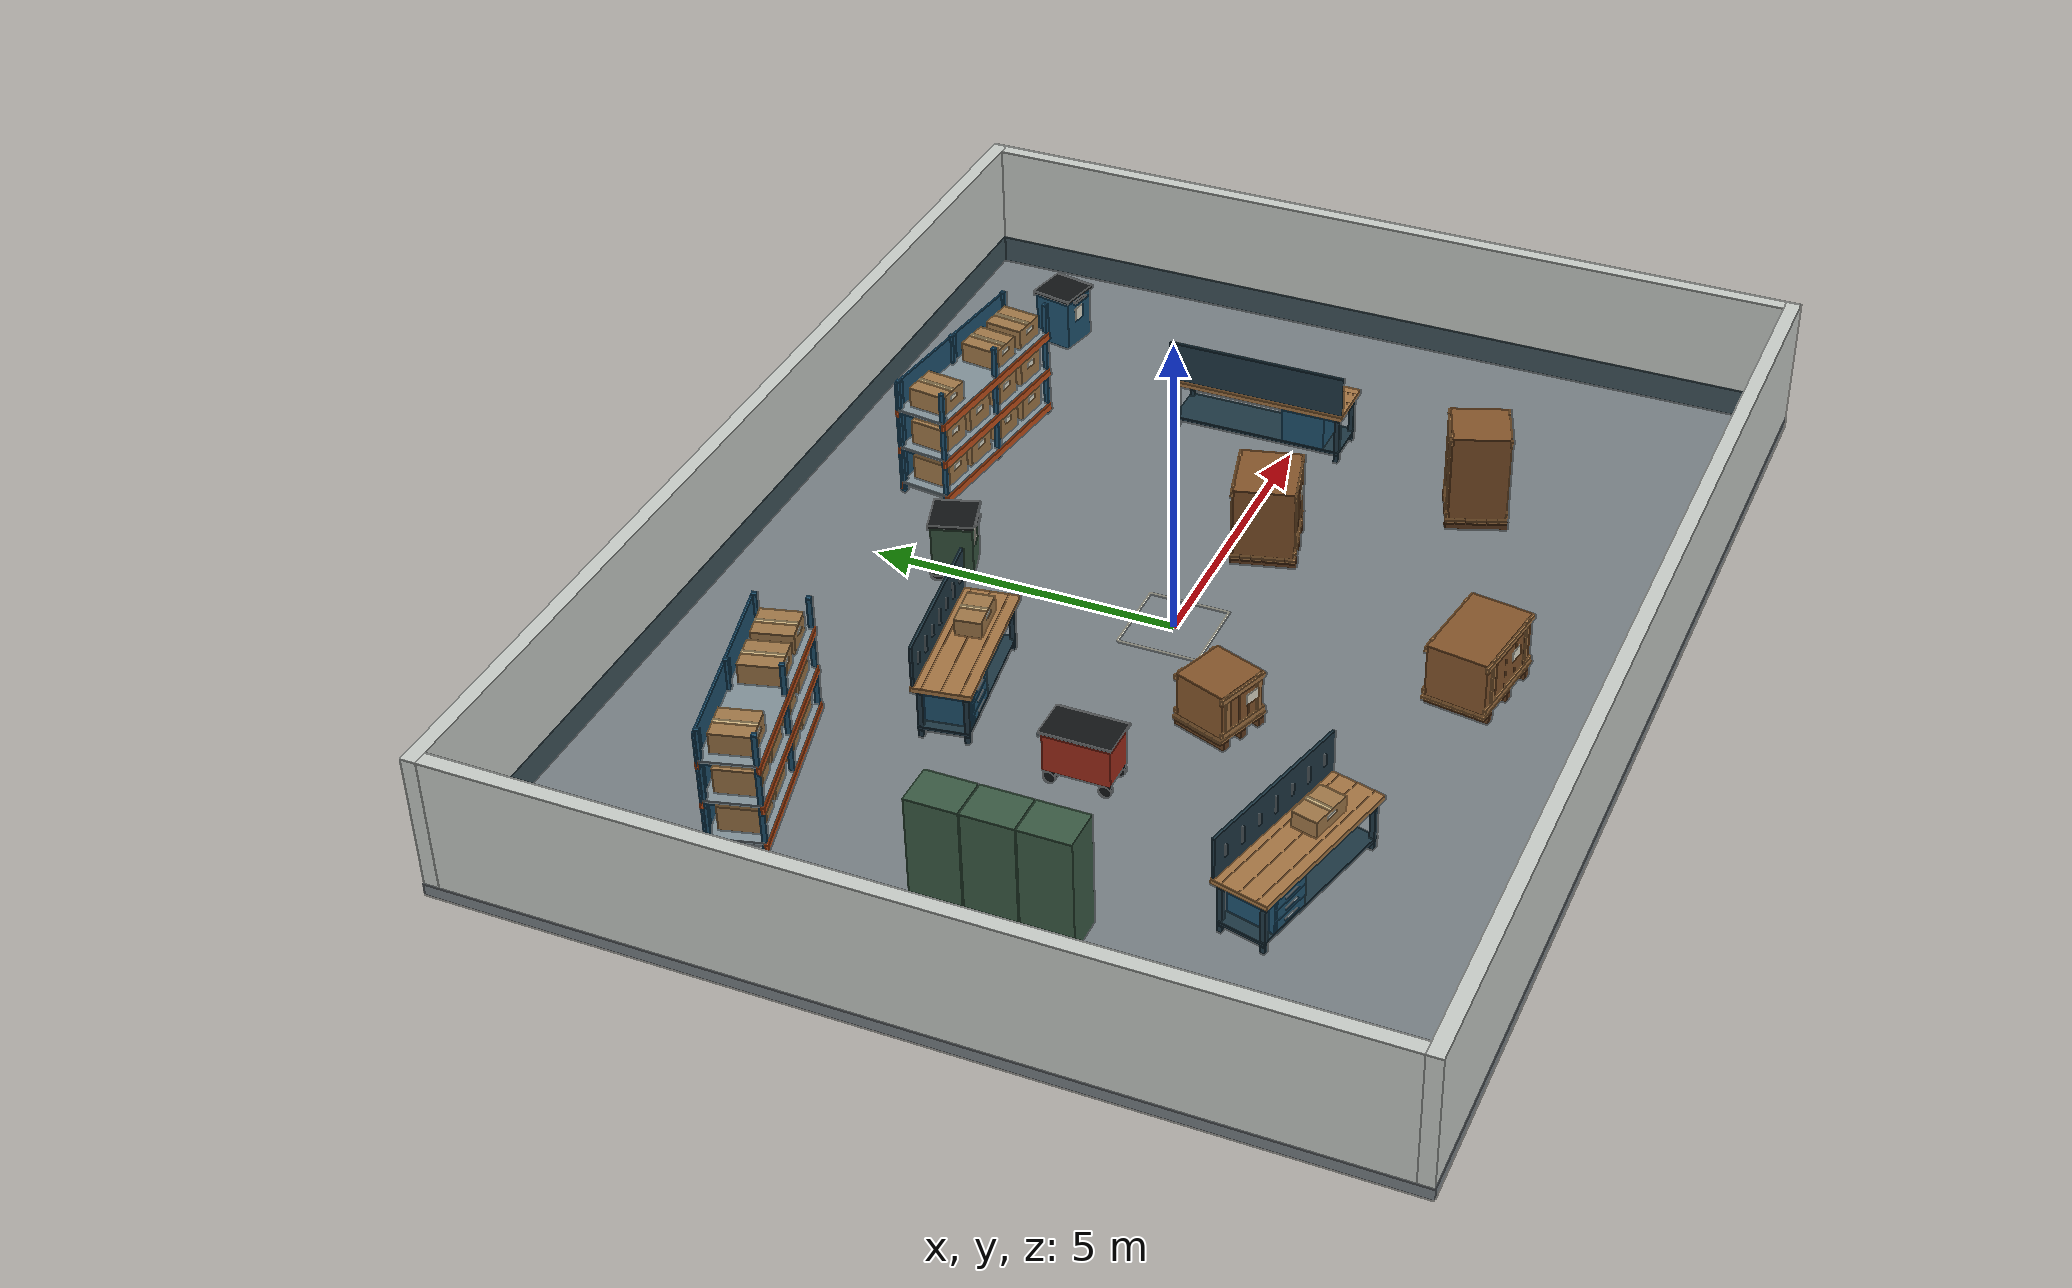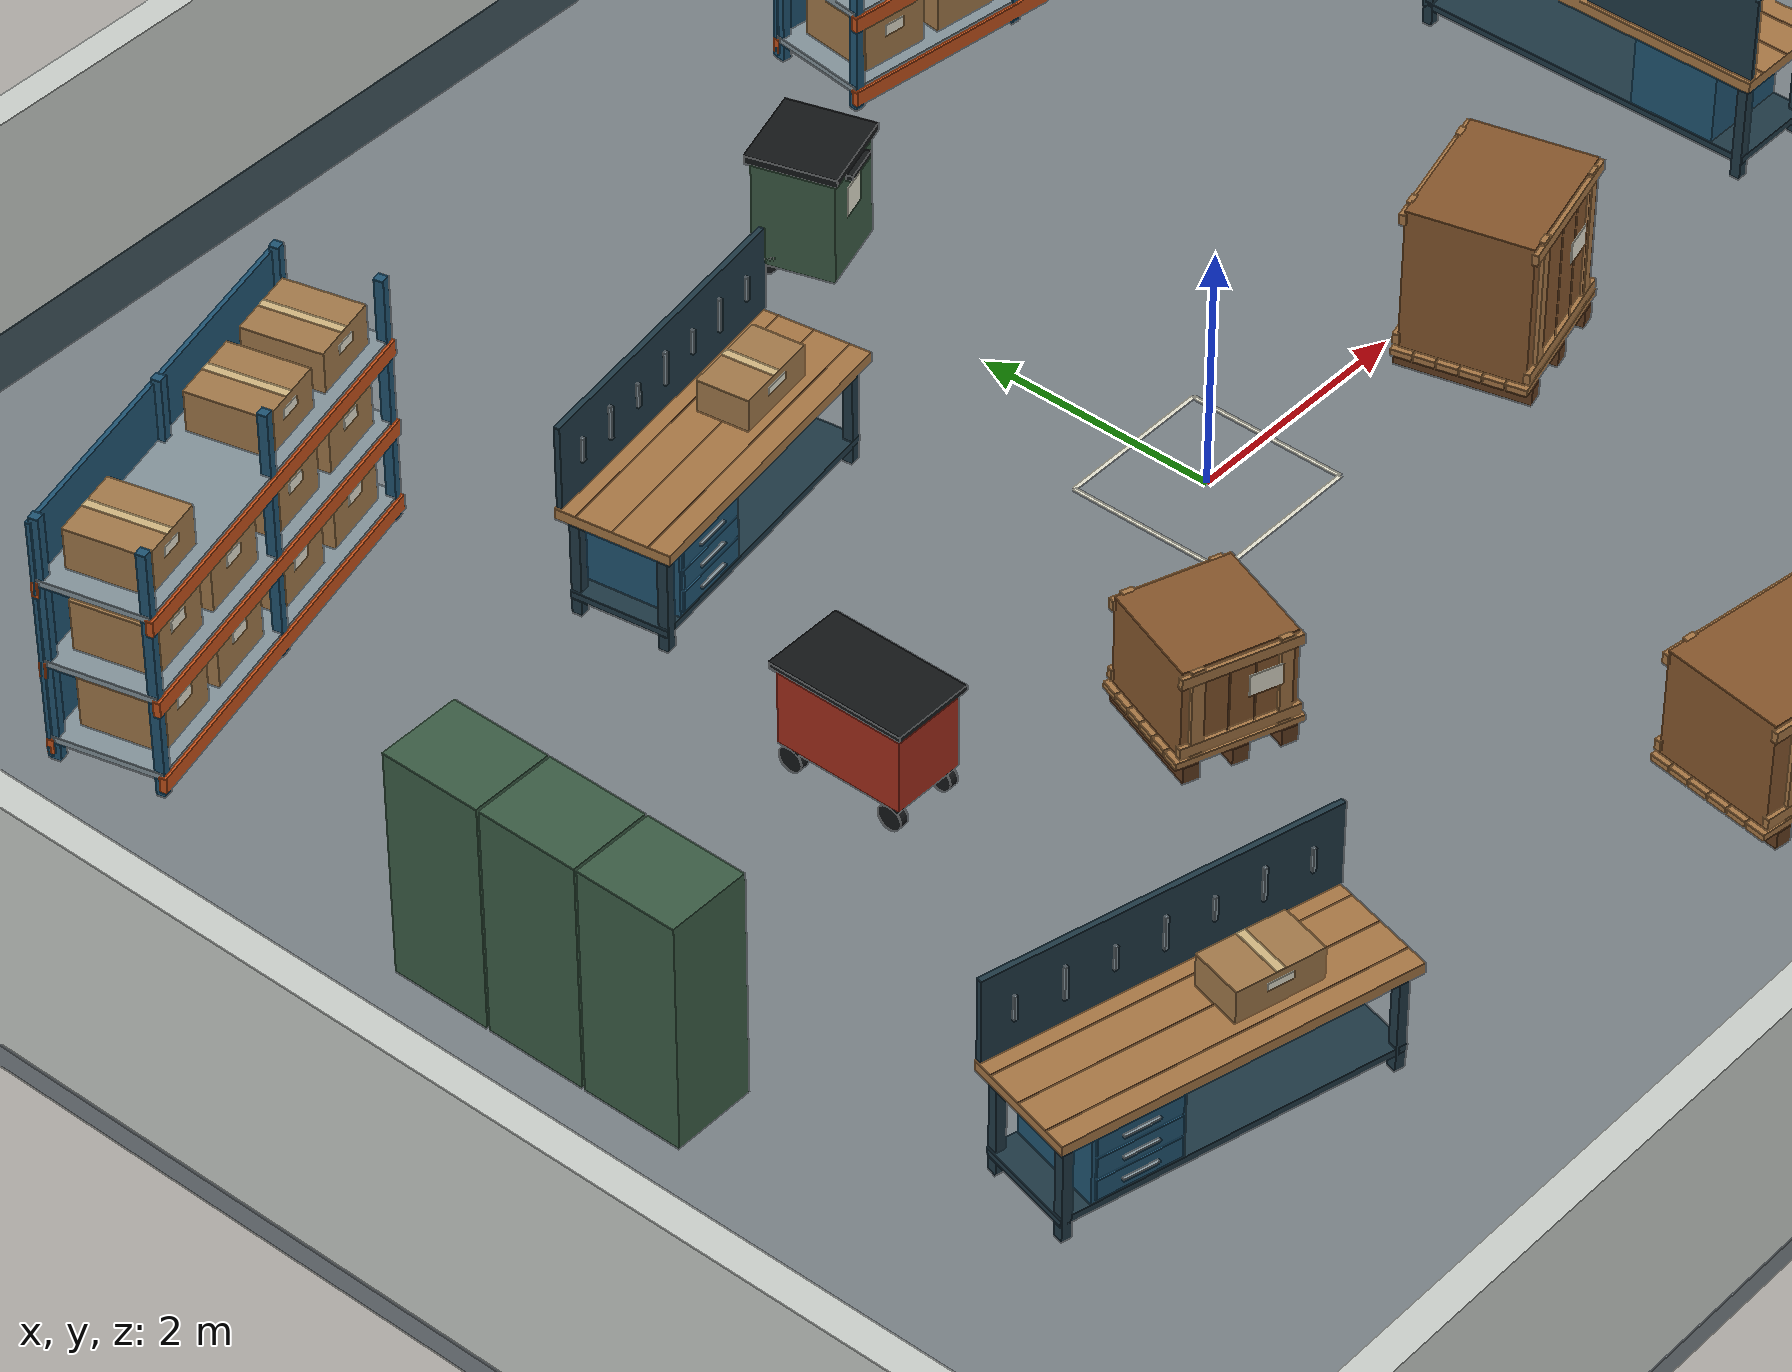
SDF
<?xml version='1.0' encoding='utf-8'?>
<sdf version="1.6">
  <world name="go2_workshop">
    <gravity>0 0 -9.8</gravity>
    <physics name="default_physics" default="true" type="ode">
      <max_step_size>.001</max_step_size>
      <real_time_factor>1</real_time_factor>
      <real_time_update_rate>1000</real_time_update_rate>
    </physics>
    <scene>
      <ambient>.62 .65 .70 1</ambient>
      <background>.80 .85 .91 1</background>
      <shadows>true</shadows>
    </scene>
    <light name="sun" type="directional">
      <pose>0 0 12 0 0 0</pose>
      <diffuse>.85 .83 .78 1</diffuse>
      <specular>.15 .15 .15 1</specular>
      <direction>-.4 .3 -1</direction>
      <cast_shadows>true</cast_shadows>
    </light>
    <light name="sky_fill" type="directional">
      <diffuse>.28 .32 .38 1</diffuse>
      <specular>0 0 0 1</specular>
      <direction>.6 -.4 -1</direction>
      <cast_shadows>false</cast_shadows>
    </light>
    <model name="floor">
      <static>true</static>
      <pose>0 0 0 0 0 0</pose>
      <link name="body">
        <collision name="concrete_slab_collision">
          <pose>0 0 -0.1 0 0 0</pose>
          <geometry>
            <box>
              <size>18.5 14.5 0.2</size>
            </box>
          </geometry>
          <surface>
            <friction>
              <ode>
                <mu>1</mu>
                <mu2>1</mu2>
              </ode>
            </friction>
          </surface>
        </collision>
        <visual name="concrete_slab">
          <pose>0 0 -0.1 0 0 0</pose>
          <geometry>
            <box>
              <size>18.5 14.5 0.2</size>
            </box>
          </geometry>
          <material>
            <ambient>0.48 0.51 0.53 1</ambient>
            <diffuse>0.48 0.51 0.53 1</diffuse>
            <specular>.08 .08 .08 1</specular>
          </material>
        </visual>
      </link>
    </model>
    <model name="perimeter_walls">
      <static>true</static>
      <pose>0 0 0 0 0 0</pose>
      <link name="body">
        <collision name="north_collision">
          <pose>0 7.12 1.1 0 0 0</pose>
          <geometry>
            <box>
              <size>18.48 0.24 2.2</size>
            </box>
          </geometry>
        </collision>
        <visual name="north">
          <pose>0 7.12 1.1 0 0 0</pose>
          <geometry>
            <box>
              <size>18.48 0.24 2.2</size>
            </box>
          </geometry>
          <material>
            <ambient>0.8 0.82 0.8 1</ambient>
            <diffuse>0.8 0.82 0.8 1</diffuse>
            <specular>.08 .08 .08 1</specular>
          </material>
        </visual>
        <visual name="north_paint">
          <pose>0 6.998 0.24 0 0 0</pose>
          <geometry>
            <box>
              <size>18 0.004 0.48</size>
            </box>
          </geometry>
          <material>
            <ambient>0.25 0.33 0.36 1</ambient>
            <diffuse>0.25 0.33 0.36 1</diffuse>
            <specular>.08 .08 .08 1</specular>
          </material>
          <cast_shadows>false</cast_shadows>
        </visual>
        <collision name="south_collision">
          <pose>0 -7.12 1.1 0 0 0</pose>
          <geometry>
            <box>
              <size>18.48 0.24 2.2</size>
            </box>
          </geometry>
        </collision>
        <visual name="south">
          <pose>0 -7.12 1.1 0 0 0</pose>
          <geometry>
            <box>
              <size>18.48 0.24 2.2</size>
            </box>
          </geometry>
          <material>
            <ambient>0.8 0.82 0.8 1</ambient>
            <diffuse>0.8 0.82 0.8 1</diffuse>
            <specular>.08 .08 .08 1</specular>
          </material>
        </visual>
        <visual name="south_paint">
          <pose>0 -6.998 0.24 0 0 0</pose>
          <geometry>
            <box>
              <size>18 0.004 0.48</size>
            </box>
          </geometry>
          <material>
            <ambient>0.25 0.33 0.36 1</ambient>
            <diffuse>0.25 0.33 0.36 1</diffuse>
            <specular>.08 .08 .08 1</specular>
          </material>
          <cast_shadows>false</cast_shadows>
        </visual>
        <collision name="west_collision">
          <pose>-9.12 0 1.1 0 0 0</pose>
          <geometry>
            <box>
              <size>0.24 14 2.2</size>
            </box>
          </geometry>
        </collision>
        <visual name="west">
          <pose>-9.12 0 1.1 0 0 0</pose>
          <geometry>
            <box>
              <size>0.24 14 2.2</size>
            </box>
          </geometry>
          <material>
            <ambient>0.8 0.82 0.8 1</ambient>
            <diffuse>0.8 0.82 0.8 1</diffuse>
            <specular>.08 .08 .08 1</specular>
          </material>
        </visual>
        <visual name="west_paint">
          <pose>-8.998 0 0.24 0 0 0</pose>
          <geometry>
            <box>
              <size>0.004 14 0.48</size>
            </box>
          </geometry>
          <material>
            <ambient>0.25 0.33 0.36 1</ambient>
            <diffuse>0.25 0.33 0.36 1</diffuse>
            <specular>.08 .08 .08 1</specular>
          </material>
          <cast_shadows>false</cast_shadows>
        </visual>
        <collision name="east_collision">
          <pose>9.12 0 1.1 0 0 0</pose>
          <geometry>
            <box>
              <size>0.24 14 2.2</size>
            </box>
          </geometry>
        </collision>
        <visual name="east">
          <pose>9.12 0 1.1 0 0 0</pose>
          <geometry>
            <box>
              <size>0.24 14 2.2</size>
            </box>
          </geometry>
          <material>
            <ambient>0.8 0.82 0.8 1</ambient>
            <diffuse>0.8 0.82 0.8 1</diffuse>
            <specular>.08 .08 .08 1</specular>
          </material>
        </visual>
        <visual name="east_paint">
          <pose>8.998 0 0.24 0 0 0</pose>
          <geometry>
            <box>
              <size>0.004 14 0.48</size>
            </box>
          </geometry>
          <material>
            <ambient>0.25 0.33 0.36 1</ambient>
            <diffuse>0.25 0.33 0.36 1</diffuse>
            <specular>.08 .08 .08 1</specular>
          </material>
          <cast_shadows>false</cast_shadows>
        </visual>
      </link>
    </model>
    <model name="floor_markings">
      <static>true</static>
      <pose>0 0 0 0 0 0</pose>
      <link name="body">
        <visual name="spawn_0">
          <pose>-0.65 0 0.003 0 0 0</pose>
          <geometry>
            <box>
              <size>0.035 1.3 0.004</size>
            </box>
          </geometry>
          <material>
            <ambient>0.9 0.89 0.82 1</ambient>
            <diffuse>0.9 0.89 0.82 1</diffuse>
            <specular>.08 .08 .08 1</specular>
          </material>
          <cast_shadows>false</cast_shadows>
        </visual>
        <visual name="spawn_1">
          <pose>0.65 0 0.003 0 0 0</pose>
          <geometry>
            <box>
              <size>0.035 1.3 0.004</size>
            </box>
          </geometry>
          <material>
            <ambient>0.9 0.89 0.82 1</ambient>
            <diffuse>0.9 0.89 0.82 1</diffuse>
            <specular>.08 .08 .08 1</specular>
          </material>
          <cast_shadows>false</cast_shadows>
        </visual>
        <visual name="spawn_2">
          <pose>0 -0.65 0.003 0 0 0</pose>
          <geometry>
            <box>
              <size>1.3 0.035 0.004</size>
            </box>
          </geometry>
          <material>
            <ambient>0.9 0.89 0.82 1</ambient>
            <diffuse>0.9 0.89 0.82 1</diffuse>
            <specular>.08 .08 .08 1</specular>
          </material>
          <cast_shadows>false</cast_shadows>
        </visual>
        <visual name="spawn_3">
          <pose>0 0.65 0.003 0 0 0</pose>
          <geometry>
            <box>
              <size>1.3 0.035 0.004</size>
            </box>
          </geometry>
          <material>
            <ambient>0.9 0.89 0.82 1</ambient>
            <diffuse>0.9 0.89 0.82 1</diffuse>
            <specular>.08 .08 .08 1</specular>
          </material>
          <cast_shadows>false</cast_shadows>
        </visual>
      </link>
    </model>
    <model name="storage_rack_west">
      <static>true</static>
      <pose>-5.5 4.0 0 0 0 0.250000</pose>
      <link name="body">
        <collision name="upright_0_0_collision">
          <pose>-1.55 -0.4 1.05 0 0 0</pose>
          <geometry>
            <box>
              <size>0.075 0.075 2.1</size>
            </box>
          </geometry>
        </collision>
        <visual name="upright_0_0">
          <pose>-1.55 -0.4 1.05 0 0 0</pose>
          <geometry>
            <box>
              <size>0.075 0.075 2.1</size>
            </box>
          </geometry>
          <material>
            <ambient>0.12 0.33 0.45 1</ambient>
            <diffuse>0.12 0.33 0.45 1</diffuse>
            <specular>.08 .08 .08 1</specular>
          </material>
        </visual>
        <collision name="upright_0_1_collision">
          <pose>-1.55 0.4 1.05 0 0 0</pose>
          <geometry>
            <box>
              <size>0.075 0.075 2.1</size>
            </box>
          </geometry>
        </collision>
        <visual name="upright_0_1">
          <pose>-1.55 0.4 1.05 0 0 0</pose>
          <geometry>
            <box>
              <size>0.075 0.075 2.1</size>
            </box>
          </geometry>
          <material>
            <ambient>0.12 0.33 0.45 1</ambient>
            <diffuse>0.12 0.33 0.45 1</diffuse>
            <specular>.08 .08 .08 1</specular>
          </material>
        </visual>
        <collision name="upright_1_0_collision">
          <pose>0 -0.4 1.05 0 0 0</pose>
          <geometry>
            <box>
              <size>0.075 0.075 2.1</size>
            </box>
          </geometry>
        </collision>
        <visual name="upright_1_0">
          <pose>0 -0.4 1.05 0 0 0</pose>
          <geometry>
            <box>
              <size>0.075 0.075 2.1</size>
            </box>
          </geometry>
          <material>
            <ambient>0.12 0.33 0.45 1</ambient>
            <diffuse>0.12 0.33 0.45 1</diffuse>
            <specular>.08 .08 .08 1</specular>
          </material>
        </visual>
        <collision name="upright_1_1_collision">
          <pose>0 0.4 1.05 0 0 0</pose>
          <geometry>
            <box>
              <size>0.075 0.075 2.1</size>
            </box>
          </geometry>
        </collision>
        <visual name="upright_1_1">
          <pose>0 0.4 1.05 0 0 0</pose>
          <geometry>
            <box>
              <size>0.075 0.075 2.1</size>
            </box>
          </geometry>
          <material>
            <ambient>0.12 0.33 0.45 1</ambient>
            <diffuse>0.12 0.33 0.45 1</diffuse>
            <specular>.08 .08 .08 1</specular>
          </material>
        </visual>
        <collision name="upright_2_0_collision">
          <pose>1.55 -0.4 1.05 0 0 0</pose>
          <geometry>
            <box>
              <size>0.075 0.075 2.1</size>
            </box>
          </geometry>
        </collision>
        <visual name="upright_2_0">
          <pose>1.55 -0.4 1.05 0 0 0</pose>
          <geometry>
            <box>
              <size>0.075 0.075 2.1</size>
            </box>
          </geometry>
          <material>
            <ambient>0.12 0.33 0.45 1</ambient>
            <diffuse>0.12 0.33 0.45 1</diffuse>
            <specular>.08 .08 .08 1</specular>
          </material>
        </visual>
        <collision name="upright_2_1_collision">
          <pose>1.55 0.4 1.05 0 0 0</pose>
          <geometry>
            <box>
              <size>0.075 0.075 2.1</size>
            </box>
          </geometry>
        </collision>
        <visual name="upright_2_1">
          <pose>1.55 0.4 1.05 0 0 0</pose>
          <geometry>
            <box>
              <size>0.075 0.075 2.1</size>
            </box>
          </geometry>
          <material>
            <ambient>0.12 0.33 0.45 1</ambient>
            <diffuse>0.12 0.33 0.45 1</diffuse>
            <specular>.08 .08 .08 1</specular>
          </material>
        </visual>
        <collision name="shelf_0_collision">
          <pose>0 0 0.18 0 0 0</pose>
          <geometry>
            <box>
              <size>3.18 0.87 0.055</size>
            </box>
          </geometry>
        </collision>
        <visual name="shelf_0">
          <pose>0 0 0.18 0 0 0</pose>
          <geometry>
            <box>
              <size>3.18 0.87 0.055</size>
            </box>
          </geometry>
          <material>
            <ambient>0.52 0.58 0.61 1</ambient>
            <diffuse>0.52 0.58 0.61 1</diffuse>
            <specular>.08 .08 .08 1</specular>
          </material>
        </visual>
        <collision name="beam_0_0_collision">
          <pose>0 -0.43 0.115 0 0 0</pose>
          <geometry>
            <box>
              <size>3.2 0.055 0.13</size>
            </box>
          </geometry>
        </collision>
        <visual name="beam_0_0">
          <pose>0 -0.43 0.115 0 0 0</pose>
          <geometry>
            <box>
              <size>3.2 0.055 0.13</size>
            </box>
          </geometry>
          <material>
            <ambient>0.78 0.32 0.1 1</ambient>
            <diffuse>0.78 0.32 0.1 1</diffuse>
            <specular>.08 .08 .08 1</specular>
          </material>
        </visual>
        <collision name="beam_0_1_collision">
          <pose>0 0.43 0.115 0 0 0</pose>
          <geometry>
            <box>
              <size>3.2 0.055 0.13</size>
            </box>
          </geometry>
        </collision>
        <visual name="beam_0_1">
          <pose>0 0.43 0.115 0 0 0</pose>
          <geometry>
            <box>
              <size>3.2 0.055 0.13</size>
            </box>
          </geometry>
          <material>
            <ambient>0.78 0.32 0.1 1</ambient>
            <diffuse>0.78 0.32 0.1 1</diffuse>
            <specular>.08 .08 .08 1</specular>
          </material>
        </visual>
        <collision name="shelf_1_collision">
          <pose>0 0 0.85 0 0 0</pose>
          <geometry>
            <box>
              <size>3.18 0.87 0.055</size>
            </box>
          </geometry>
        </collision>
        <visual name="shelf_1">
          <pose>0 0 0.85 0 0 0</pose>
          <geometry>
            <box>
              <size>3.18 0.87 0.055</size>
            </box>
          </geometry>
          <material>
            <ambient>0.52 0.58 0.61 1</ambient>
            <diffuse>0.52 0.58 0.61 1</diffuse>
            <specular>.08 .08 .08 1</specular>
          </material>
        </visual>
        <collision name="beam_1_0_collision">
          <pose>0 -0.43 0.785 0 0 0</pose>
          <geometry>
            <box>
              <size>3.2 0.055 0.13</size>
            </box>
          </geometry>
        </collision>
        <visual name="beam_1_0">
          <pose>0 -0.43 0.785 0 0 0</pose>
          <geometry>
            <box>
              <size>3.2 0.055 0.13</size>
            </box>
          </geometry>
          <material>
            <ambient>0.78 0.32 0.1 1</ambient>
            <diffuse>0.78 0.32 0.1 1</diffuse>
            <specular>.08 .08 .08 1</specular>
          </material>
        </visual>
        <collision name="beam_1_1_collision">
          <pose>0 0.43 0.785 0 0 0</pose>
          <geometry>
            <box>
              <size>3.2 0.055 0.13</size>
            </box>
          </geometry>
        </collision>
        <visual name="beam_1_1">
          <pose>0 0.43 0.785 0 0 0</pose>
          <geometry>
            <box>
              <size>3.2 0.055 0.13</size>
            </box>
          </geometry>
          <material>
            <ambient>0.78 0.32 0.1 1</ambient>
            <diffuse>0.78 0.32 0.1 1</diffuse>
            <specular>.08 .08 .08 1</specular>
          </material>
        </visual>
        <collision name="shelf_2_collision">
          <pose>0 0 1.55 0 0 0</pose>
          <geometry>
            <box>
              <size>3.18 0.87 0.055</size>
            </box>
          </geometry>
        </collision>
        <visual name="shelf_2">
          <pose>0 0 1.55 0 0 0</pose>
          <geometry>
            <box>
              <size>3.18 0.87 0.055</size>
            </box>
          </geometry>
          <material>
            <ambient>0.52 0.58 0.61 1</ambient>
            <diffuse>0.52 0.58 0.61 1</diffuse>
            <specular>.08 .08 .08 1</specular>
          </material>
        </visual>
        <collision name="beam_2_0_collision">
          <pose>0 -0.43 1.485 0 0 0</pose>
          <geometry>
            <box>
              <size>3.2 0.055 0.13</size>
            </box>
          </geometry>
        </collision>
        <visual name="beam_2_0">
          <pose>0 -0.43 1.485 0 0 0</pose>
          <geometry>
            <box>
              <size>3.2 0.055 0.13</size>
            </box>
          </geometry>
          <material>
            <ambient>0.78 0.32 0.1 1</ambient>
            <diffuse>0.78 0.32 0.1 1</diffuse>
            <specular>.08 .08 .08 1</specular>
          </material>
        </visual>
        <collision name="beam_2_1_collision">
          <pose>0 0.43 1.485 0 0 0</pose>
          <geometry>
            <box>
              <size>3.2 0.055 0.13</size>
            </box>
          </geometry>
        </collision>
        <visual name="beam_2_1">
          <pose>0 0.43 1.485 0 0 0</pose>
          <geometry>
            <box>
              <size>3.2 0.055 0.13</size>
            </box>
          </geometry>
          <material>
            <ambient>0.78 0.32 0.1 1</ambient>
            <diffuse>0.78 0.32 0.1 1</diffuse>
            <specular>.08 .08 .08 1</specular>
          </material>
        </visual>
        <collision name="back_panel_collision">
          <pose>0 0.435 1.04 0 0 0</pose>
          <geometry>
            <box>
              <size>3.2 0.035 2.04</size>
            </box>
          </geometry>
        </collision>
        <visual name="back_panel">
          <pose>0 0.435 1.04 0 0 0</pose>
          <geometry>
            <box>
              <size>3.2 0.035 2.04</size>
            </box>
          </geometry>
          <material>
            <ambient>0.12 0.33 0.45 1</ambient>
            <diffuse>0.12 0.33 0.45 1</diffuse>
            <specular>.08 .08 .08 1</specular>
          </material>
        </visual>
        <collision name="box_0_0_collision">
          <pose>-1.12 -0.015 0.418 0 0 0</pose>
          <geometry>
            <box>
              <size>0.58 0.64 0.42</size>
            </box>
          </geometry>
        </collision>
        <visual name="box_0_0">
          <pose>-1.12 -0.015 0.418 0 0 0</pose>
          <geometry>
            <box>
              <size>0.58 0.64 0.42</size>
            </box>
          </geometry>
          <material>
            <ambient>0.64 0.48 0.29 1</ambient>
            <diffuse>0.64 0.48 0.29 1</diffuse>
            <specular>.08 .08 .08 1</specular>
          </material>
        </visual>
        <visual name="box_0_0_tape">
          <pose>-1.12 -0.015 0.629 0 0 0</pose>
          <geometry>
            <box>
              <size>0.07 0.64 0.002</size>
            </box>
          </geometry>
          <material>
            <ambient>0.83 0.72 0.51 1</ambient>
            <diffuse>0.83 0.72 0.51 1</diffuse>
            <specular>.08 .08 .08 1</specular>
          </material>
          <cast_shadows>false</cast_shadows>
        </visual>
        <visual name="box_0_0_label">
          <pose>-1.12 -0.337 0.481 0 0 0</pose>
          <geometry>
            <box>
              <size>0.174 0.003 0.0966</size>
            </box>
          </geometry>
          <material>
            <ambient>0.9 0.89 0.82 1</ambient>
            <diffuse>0.9 0.89 0.82 1</diffuse>
            <specular>.08 .08 .08 1</specular>
          </material>
          <cast_shadows>false</cast_shadows>
        </visual>
        <collision name="box_0_1_collision">
          <pose>-0.4 -0.015 0.418 0 0 0</pose>
          <geometry>
            <box>
              <size>0.58 0.64 0.42</size>
            </box>
          </geometry>
        </collision>
        <visual name="box_0_1">
          <pose>-0.4 -0.015 0.418 0 0 0</pose>
          <geometry>
            <box>
              <size>0.58 0.64 0.42</size>
            </box>
          </geometry>
          <material>
            <ambient>0.64 0.48 0.29 1</ambient>
            <diffuse>0.64 0.48 0.29 1</diffuse>
            <specular>.08 .08 .08 1</specular>
          </material>
        </visual>
        <visual name="box_0_1_tape">
          <pose>-0.4 -0.015 0.629 0 0 0</pose>
          <geometry>
            <box>
              <size>0.07 0.64 0.002</size>
            </box>
          </geometry>
          <material>
            <ambient>0.83 0.72 0.51 1</ambient>
            <diffuse>0.83 0.72 0.51 1</diffuse>
            <specular>.08 .08 .08 1</specular>
          </material>
          <cast_shadows>false</cast_shadows>
        </visual>
        <visual name="box_0_1_label">
          <pose>-0.4 -0.337 0.481 0 0 0</pose>
          <geometry>
            <box>
              <size>0.174 0.003 0.0966</size>
            </box>
          </geometry>
          <material>
            <ambient>0.9 0.89 0.82 1</ambient>
            <diffuse>0.9 0.89 0.82 1</diffuse>
            <specular>.08 .08 .08 1</specular>
          </material>
          <cast_shadows>false</cast_shadows>
        </visual>
        <collision name="box_0_2_collision">
          <pose>0.42 -0.015 0.418 0 0 0</pose>
          <geometry>
            <box>
              <size>0.58 0.64 0.42</size>
            </box>
          </geometry>
        </collision>
        <visual name="box_0_2">
          <pose>0.42 -0.015 0.418 0 0 0</pose>
          <geometry>
            <box>
              <size>0.58 0.64 0.42</size>
            </box>
          </geometry>
          <material>
            <ambient>0.64 0.48 0.29 1</ambient>
            <diffuse>0.64 0.48 0.29 1</diffuse>
            <specular>.08 .08 .08 1</specular>
          </material>
        </visual>
        <visual name="box_0_2_tape">
          <pose>0.42 -0.015 0.629 0 0 0</pose>
          <geometry>
            <box>
              <size>0.07 0.64 0.002</size>
            </box>
          </geometry>
          <material>
            <ambient>0.83 0.72 0.51 1</ambient>
            <diffuse>0.83 0.72 0.51 1</diffuse>
            <specular>.08 .08 .08 1</specular>
          </material>
          <cast_shadows>false</cast_shadows>
        </visual>
        <visual name="box_0_2_label">
          <pose>0.42 -0.337 0.481 0 0 0</pose>
          <geometry>
            <box>
              <size>0.174 0.003 0.0966</size>
            </box>
          </geometry>
          <material>
            <ambient>0.9 0.89 0.82 1</ambient>
            <diffuse>0.9 0.89 0.82 1</diffuse>
            <specular>.08 .08 .08 1</specular>
          </material>
          <cast_shadows>false</cast_shadows>
        </visual>
        <collision name="box_0_3_collision">
          <pose>1.16 -0.015 0.418 0 0 0</pose>
          <geometry>
            <box>
              <size>0.58 0.64 0.42</size>
            </box>
          </geometry>
        </collision>
        <visual name="box_0_3">
          <pose>1.16 -0.015 0.418 0 0 0</pose>
          <geometry>
            <box>
              <size>0.58 0.64 0.42</size>
            </box>
          </geometry>
          <material>
            <ambient>0.64 0.48 0.29 1</ambient>
            <diffuse>0.64 0.48 0.29 1</diffuse>
            <specular>.08 .08 .08 1</specular>
          </material>
        </visual>
        <visual name="box_0_3_tape">
          <pose>1.16 -0.015 0.629 0 0 0</pose>
          <geometry>
            <box>
              <size>0.07 0.64 0.002</size>
            </box>
          </geometry>
          <material>
            <ambient>0.83 0.72 0.51 1</ambient>
            <diffuse>0.83 0.72 0.51 1</diffuse>
            <specular>.08 .08 .08 1</specular>
          </material>
          <cast_shadows>false</cast_shadows>
        </visual>
        <visual name="box_0_3_label">
          <pose>1.16 -0.337 0.481 0 0 0</pose>
          <geometry>
            <box>
              <size>0.174 0.003 0.0966</size>
            </box>
          </geometry>
          <material>
            <ambient>0.9 0.89 0.82 1</ambient>
            <diffuse>0.9 0.89 0.82 1</diffuse>
            <specular>.08 .08 .08 1</specular>
          </material>
          <cast_shadows>false</cast_shadows>
        </visual>
        <collision name="box_1_0_collision">
          <pose>-1.12 -0.015 1.088 0 0 0</pose>
          <geometry>
            <box>
              <size>0.58 0.64 0.42</size>
            </box>
          </geometry>
        </collision>
        <visual name="box_1_0">
          <pose>-1.12 -0.015 1.088 0 0 0</pose>
          <geometry>
            <box>
              <size>0.58 0.64 0.42</size>
            </box>
          </geometry>
          <material>
            <ambient>0.64 0.48 0.29 1</ambient>
            <diffuse>0.64 0.48 0.29 1</diffuse>
            <specular>.08 .08 .08 1</specular>
          </material>
        </visual>
        <visual name="box_1_0_tape">
          <pose>-1.12 -0.015 1.299 0 0 0</pose>
          <geometry>
            <box>
              <size>0.07 0.64 0.002</size>
            </box>
          </geometry>
          <material>
            <ambient>0.83 0.72 0.51 1</ambient>
            <diffuse>0.83 0.72 0.51 1</diffuse>
            <specular>.08 .08 .08 1</specular>
          </material>
          <cast_shadows>false</cast_shadows>
        </visual>
        <visual name="box_1_0_label">
          <pose>-1.12 -0.337 1.151 0 0 0</pose>
          <geometry>
            <box>
              <size>0.174 0.003 0.0966</size>
            </box>
          </geometry>
          <material>
            <ambient>0.9 0.89 0.82 1</ambient>
            <diffuse>0.9 0.89 0.82 1</diffuse>
            <specular>.08 .08 .08 1</specular>
          </material>
          <cast_shadows>false</cast_shadows>
        </visual>
        <collision name="box_1_1_collision">
          <pose>-0.4 -0.015 1.088 0 0 0</pose>
          <geometry>
            <box>
              <size>0.58 0.64 0.42</size>
            </box>
          </geometry>
        </collision>
        <visual name="box_1_1">
          <pose>-0.4 -0.015 1.088 0 0 0</pose>
          <geometry>
            <box>
              <size>0.58 0.64 0.42</size>
            </box>
          </geometry>
          <material>
            <ambient>0.64 0.48 0.29 1</ambient>
            <diffuse>0.64 0.48 0.29 1</diffuse>
            <specular>.08 .08 .08 1</specular>
          </material>
        </visual>
        <visual name="box_1_1_tape">
          <pose>-0.4 -0.015 1.299 0 0 0</pose>
          <geometry>
            <box>
              <size>0.07 0.64 0.002</size>
            </box>
          </geometry>
          <material>
            <ambient>0.83 0.72 0.51 1</ambient>
            <diffuse>0.83 0.72 0.51 1</diffuse>
            <specular>.08 .08 .08 1</specular>
          </material>
          <cast_shadows>false</cast_shadows>
        </visual>
        <visual name="box_1_1_label">
          <pose>-0.4 -0.337 1.151 0 0 0</pose>
          <geometry>
            <box>
              <size>0.174 0.003 0.0966</size>
            </box>
          </geometry>
          <material>
            <ambient>0.9 0.89 0.82 1</ambient>
            <diffuse>0.9 0.89 0.82 1</diffuse>
            <specular>.08 .08 .08 1</specular>
          </material>
          <cast_shadows>false</cast_shadows>
        </visual>
        <collision name="box_1_2_collision">
          <pose>0.42 -0.015 1.088 0 0 0</pose>
          <geometry>
            <box>
              <size>0.58 0.64 0.42</size>
            </box>
          </geometry>
        </collision>
        <visual name="box_1_2">
          <pose>0.42 -0.015 1.088 0 0 0</pose>
          <geometry>
            <box>
              <size>0.58 0.64 0.42</size>
            </box>
          </geometry>
          <material>
            <ambient>0.64 0.48 0.29 1</ambient>
            <diffuse>0.64 0.48 0.29 1</diffuse>
            <specular>.08 .08 .08 1</specular>
          </material>
        </visual>
        <visual name="box_1_2_tape">
          <pose>0.42 -0.015 1.299 0 0 0</pose>
          <geometry>
            <box>
              <size>0.07 0.64 0.002</size>
            </box>
          </geometry>
          <material>
            <ambient>0.83 0.72 0.51 1</ambient>
            <diffuse>0.83 0.72 0.51 1</diffuse>
            <specular>.08 .08 .08 1</specular>
          </material>
          <cast_shadows>false</cast_shadows>
        </visual>
        <visual name="box_1_2_label">
          <pose>0.42 -0.337 1.151 0 0 0</pose>
          <geometry>
            <box>
              <size>0.174 0.003 0.0966</size>
            </box>
          </geometry>
          <material>
            <ambient>0.9 0.89 0.82 1</ambient>
            <diffuse>0.9 0.89 0.82 1</diffuse>
            <specular>.08 .08 .08 1</specular>
          </material>
          <cast_shadows>false</cast_shadows>
        </visual>
        <collision name="box_1_3_collision">
          <pose>1.16 -0.015 1.088 0 0 0</pose>
          <geometry>
            <box>
              <size>0.58 0.64 0.42</size>
            </box>
          </geometry>
        </collision>
        <visual name="box_1_3">
          <pose>1.16 -0.015 1.088 0 0 0</pose>
          <geometry>
            <box>
              <size>0.58 0.64 0.42</size>
            </box>
          </geometry>
          <material>
            <ambient>0.64 0.48 0.29 1</ambient>
            <diffuse>0.64 0.48 0.29 1</diffuse>
            <specular>.08 .08 .08 1</specular>
          </material>
        </visual>
        <visual name="box_1_3_tape">
          <pose>1.16 -0.015 1.299 0 0 0</pose>
          <geometry>
            <box>
              <size>0.07 0.64 0.002</size>
            </box>
          </geometry>
          <material>
            <ambient>0.83 0.72 0.51 1</ambient>
            <diffuse>0.83 0.72 0.51 1</diffuse>
            <specular>.08 .08 .08 1</specular>
          </material>
          <cast_shadows>false</cast_shadows>
        </visual>
        <visual name="box_1_3_label">
          <pose>1.16 -0.337 1.151 0 0 0</pose>
          <geometry>
            <box>
              <size>0.174 0.003 0.0966</size>
            </box>
          </geometry>
          <material>
            <ambient>0.9 0.89 0.82 1</ambient>
            <diffuse>0.9 0.89 0.82 1</diffuse>
            <specular>.08 .08 .08 1</specular>
          </material>
          <cast_shadows>false</cast_shadows>
        </visual>
        <collision name="box_2_0_collision">
          <pose>-1.12 -0.015 1.748 0 0 0</pose>
          <geometry>
            <box>
              <size>0.58 0.64 0.34</size>
            </box>
          </geometry>
        </collision>
        <visual name="box_2_0">
          <pose>-1.12 -0.015 1.748 0 0 0</pose>
          <geometry>
            <box>
              <size>0.58 0.64 0.34</size>
            </box>
          </geometry>
          <material>
            <ambient>0.64 0.48 0.29 1</ambient>
            <diffuse>0.64 0.48 0.29 1</diffuse>
            <specular>.08 .08 .08 1</specular>
          </material>
        </visual>
        <visual name="box_2_0_tape">
          <pose>-1.12 -0.015 1.919 0 0 0</pose>
          <geometry>
            <box>
              <size>0.07 0.64 0.002</size>
            </box>
          </geometry>
          <material>
            <ambient>0.83 0.72 0.51 1</ambient>
            <diffuse>0.83 0.72 0.51 1</diffuse>
            <specular>.08 .08 .08 1</specular>
          </material>
          <cast_shadows>false</cast_shadows>
        </visual>
        <visual name="box_2_0_label">
          <pose>-1.12 -0.337 1.799 0 0 0</pose>
          <geometry>
            <box>
              <size>0.174 0.003 0.0782</size>
            </box>
          </geometry>
          <material>
            <ambient>0.9 0.89 0.82 1</ambient>
            <diffuse>0.9 0.89 0.82 1</diffuse>
            <specular>.08 .08 .08 1</specular>
          </material>
          <cast_shadows>false</cast_shadows>
        </visual>
        <collision name="box_2_2_collision">
          <pose>0.42 -0.015 1.748 0 0 0</pose>
          <geometry>
            <box>
              <size>0.58 0.64 0.34</size>
            </box>
          </geometry>
        </collision>
        <visual name="box_2_2">
          <pose>0.42 -0.015 1.748 0 0 0</pose>
          <geometry>
            <box>
              <size>0.58 0.64 0.34</size>
            </box>
          </geometry>
          <material>
            <ambient>0.64 0.48 0.29 1</ambient>
            <diffuse>0.64 0.48 0.29 1</diffuse>
            <specular>.08 .08 .08 1</specular>
          </material>
        </visual>
        <visual name="box_2_2_tape">
          <pose>0.42 -0.015 1.919 0 0 0</pose>
          <geometry>
            <box>
              <size>0.07 0.64 0.002</size>
            </box>
          </geometry>
          <material>
            <ambient>0.83 0.72 0.51 1</ambient>
            <diffuse>0.83 0.72 0.51 1</diffuse>
            <specular>.08 .08 .08 1</specular>
          </material>
          <cast_shadows>false</cast_shadows>
        </visual>
        <visual name="box_2_2_label">
          <pose>0.42 -0.337 1.799 0 0 0</pose>
          <geometry>
            <box>
              <size>0.174 0.003 0.0782</size>
            </box>
          </geometry>
          <material>
            <ambient>0.9 0.89 0.82 1</ambient>
            <diffuse>0.9 0.89 0.82 1</diffuse>
            <specular>.08 .08 .08 1</specular>
          </material>
          <cast_shadows>false</cast_shadows>
        </visual>
        <collision name="box_2_3_collision">
          <pose>1.16 -0.015 1.748 0 0 0</pose>
          <geometry>
            <box>
              <size>0.58 0.64 0.34</size>
            </box>
          </geometry>
        </collision>
        <visual name="box_2_3">
          <pose>1.16 -0.015 1.748 0 0 0</pose>
          <geometry>
            <box>
              <size>0.58 0.64 0.34</size>
            </box>
          </geometry>
          <material>
            <ambient>0.64 0.48 0.29 1</ambient>
            <diffuse>0.64 0.48 0.29 1</diffuse>
            <specular>.08 .08 .08 1</specular>
          </material>
        </visual>
        <visual name="box_2_3_tape">
          <pose>1.16 -0.015 1.919 0 0 0</pose>
          <geometry>
            <box>
              <size>0.07 0.64 0.002</size>
            </box>
          </geometry>
          <material>
            <ambient>0.83 0.72 0.51 1</ambient>
            <diffuse>0.83 0.72 0.51 1</diffuse>
            <specular>.08 .08 .08 1</specular>
          </material>
          <cast_shadows>false</cast_shadows>
        </visual>
        <visual name="box_2_3_label">
          <pose>1.16 -0.337 1.799 0 0 0</pose>
          <geometry>
            <box>
              <size>0.174 0.003 0.0782</size>
            </box>
          </geometry>
          <material>
            <ambient>0.9 0.89 0.82 1</ambient>
            <diffuse>0.9 0.89 0.82 1</diffuse>
            <specular>.08 .08 .08 1</specular>
          </material>
          <cast_shadows>false</cast_shadows>
        </visual>
      </link>
    </model>
    <model name="storage_rack_north">
      <static>true</static>
      <pose>3.2 4.8 0 0 0 -0.120000</pose>
      <link name="body">
        <collision name="upright_0_0_collision">
          <pose>-1.55 -0.4 1.05 0 0 0</pose>
          <geometry>
            <box>
              <size>0.075 0.075 2.1</size>
            </box>
          </geometry>
        </collision>
        <visual name="upright_0_0">
          <pose>-1.55 -0.4 1.05 0 0 0</pose>
          <geometry>
            <box>
              <size>0.075 0.075 2.1</size>
            </box>
          </geometry>
          <material>
            <ambient>0.12 0.33 0.45 1</ambient>
            <diffuse>0.12 0.33 0.45 1</diffuse>
            <specular>.08 .08 .08 1</specular>
          </material>
        </visual>
        <collision name="upright_0_1_collision">
          <pose>-1.55 0.4 1.05 0 0 0</pose>
          <geometry>
            <box>
              <size>0.075 0.075 2.1</size>
            </box>
          </geometry>
        </collision>
        <visual name="upright_0_1">
          <pose>-1.55 0.4 1.05 0 0 0</pose>
          <geometry>
            <box>
              <size>0.075 0.075 2.1</size>
            </box>
          </geometry>
          <material>
            <ambient>0.12 0.33 0.45 1</ambient>
            <diffuse>0.12 0.33 0.45 1</diffuse>
            <specular>.08 .08 .08 1</specular>
          </material>
        </visual>
        <collision name="upright_1_0_collision">
          <pose>0 -0.4 1.05 0 0 0</pose>
          <geometry>
            <box>
              <size>0.075 0.075 2.1</size>
            </box>
          </geometry>
        </collision>
        <visual name="upright_1_0">
          <pose>0 -0.4 1.05 0 0 0</pose>
          <geometry>
            <box>
              <size>0.075 0.075 2.1</size>
            </box>
          </geometry>
          <material>
            <ambient>0.12 0.33 0.45 1</ambient>
            <diffuse>0.12 0.33 0.45 1</diffuse>
            <specular>.08 .08 .08 1</specular>
          </material>
        </visual>
        <collision name="upright_1_1_collision">
          <pose>0 0.4 1.05 0 0 0</pose>
          <geometry>
            <box>
              <size>0.075 0.075 2.1</size>
            </box>
          </geometry>
        </collision>
        <visual name="upright_1_1">
          <pose>0 0.4 1.05 0 0 0</pose>
          <geometry>
            <box>
              <size>0.075 0.075 2.1</size>
            </box>
          </geometry>
          <material>
            <ambient>0.12 0.33 0.45 1</ambient>
            <diffuse>0.12 0.33 0.45 1</diffuse>
            <specular>.08 .08 .08 1</specular>
          </material>
        </visual>
        <collision name="upright_2_0_collision">
          <pose>1.55 -0.4 1.05 0 0 0</pose>
          <geometry>
            <box>
              <size>0.075 0.075 2.1</size>
            </box>
          </geometry>
        </collision>
        <visual name="upright_2_0">
          <pose>1.55 -0.4 1.05 0 0 0</pose>
          <geometry>
            <box>
              <size>0.075 0.075 2.1</size>
            </box>
          </geometry>
          <material>
            <ambient>0.12 0.33 0.45 1</ambient>
            <diffuse>0.12 0.33 0.45 1</diffuse>
            <specular>.08 .08 .08 1</specular>
          </material>
        </visual>
        <collision name="upright_2_1_collision">
          <pose>1.55 0.4 1.05 0 0 0</pose>
          <geometry>
            <box>
              <size>0.075 0.075 2.1</size>
            </box>
          </geometry>
        </collision>
        <visual name="upright_2_1">
          <pose>1.55 0.4 1.05 0 0 0</pose>
          <geometry>
            <box>
              <size>0.075 0.075 2.1</size>
            </box>
          </geometry>
          <material>
            <ambient>0.12 0.33 0.45 1</ambient>
            <diffuse>0.12 0.33 0.45 1</diffuse>
            <specular>.08 .08 .08 1</specular>
          </material>
        </visual>
        <collision name="shelf_0_collision">
          <pose>0 0 0.18 0 0 0</pose>
          <geometry>
            <box>
              <size>3.18 0.87 0.055</size>
            </box>
          </geometry>
        </collision>
        <visual name="shelf_0">
          <pose>0 0 0.18 0 0 0</pose>
          <geometry>
            <box>
              <size>3.18 0.87 0.055</size>
            </box>
          </geometry>
          <material>
            <ambient>0.52 0.58 0.61 1</ambient>
            <diffuse>0.52 0.58 0.61 1</diffuse>
            <specular>.08 .08 .08 1</specular>
          </material>
        </visual>
        <collision name="beam_0_0_collision">
          <pose>0 -0.43 0.115 0 0 0</pose>
          <geometry>
            <box>
              <size>3.2 0.055 0.13</size>
            </box>
          </geometry>
        </collision>
        <visual name="beam_0_0">
          <pose>0 -0.43 0.115 0 0 0</pose>
          <geometry>
            <box>
              <size>3.2 0.055 0.13</size>
            </box>
          </geometry>
          <material>
            <ambient>0.78 0.32 0.1 1</ambient>
            <diffuse>0.78 0.32 0.1 1</diffuse>
            <specular>.08 .08 .08 1</specular>
          </material>
        </visual>
        <collision name="beam_0_1_collision">
          <pose>0 0.43 0.115 0 0 0</pose>
          <geometry>
            <box>
              <size>3.2 0.055 0.13</size>
            </box>
          </geometry>
        </collision>
        <visual name="beam_0_1">
          <pose>0 0.43 0.115 0 0 0</pose>
          <geometry>
            <box>
              <size>3.2 0.055 0.13</size>
            </box>
          </geometry>
          <material>
            <ambient>0.78 0.32 0.1 1</ambient>
            <diffuse>0.78 0.32 0.1 1</diffuse>
            <specular>.08 .08 .08 1</specular>
          </material>
        </visual>
        <collision name="shelf_1_collision">
          <pose>0 0 0.85 0 0 0</pose>
          <geometry>
            <box>
              <size>3.18 0.87 0.055</size>
            </box>
          </geometry>
        </collision>
        <visual name="shelf_1">
          <pose>0 0 0.85 0 0 0</pose>
          <geometry>
            <box>
              <size>3.18 0.87 0.055</size>
            </box>
          </geometry>
          <material>
            <ambient>0.52 0.58 0.61 1</ambient>
            <diffuse>0.52 0.58 0.61 1</diffuse>
            <specular>.08 .08 .08 1</specular>
          </material>
        </visual>
        <collision name="beam_1_0_collision">
          <pose>0 -0.43 0.785 0 0 0</pose>
          <geometry>
            <box>
              <size>3.2 0.055 0.13</size>
            </box>
          </geometry>
        </collision>
        <visual name="beam_1_0">
          <pose>0 -0.43 0.785 0 0 0</pose>
          <geometry>
            <box>
              <size>3.2 0.055 0.13</size>
            </box>
          </geometry>
          <material>
            <ambient>0.78 0.32 0.1 1</ambient>
            <diffuse>0.78 0.32 0.1 1</diffuse>
            <specular>.08 .08 .08 1</specular>
          </material>
        </visual>
        <collision name="beam_1_1_collision">
          <pose>0 0.43 0.785 0 0 0</pose>
          <geometry>
            <box>
              <size>3.2 0.055 0.13</size>
            </box>
          </geometry>
        </collision>
        <visual name="beam_1_1">
          <pose>0 0.43 0.785 0 0 0</pose>
          <geometry>
            <box>
              <size>3.2 0.055 0.13</size>
            </box>
          </geometry>
          <material>
            <ambient>0.78 0.32 0.1 1</ambient>
            <diffuse>0.78 0.32 0.1 1</diffuse>
            <specular>.08 .08 .08 1</specular>
          </material>
        </visual>
        <collision name="shelf_2_collision">
          <pose>0 0 1.55 0 0 0</pose>
          <geometry>
            <box>
              <size>3.18 0.87 0.055</size>
            </box>
          </geometry>
        </collision>
        <visual name="shelf_2">
          <pose>0 0 1.55 0 0 0</pose>
          <geometry>
            <box>
              <size>3.18 0.87 0.055</size>
            </box>
          </geometry>
          <material>
            <ambient>0.52 0.58 0.61 1</ambient>
            <diffuse>0.52 0.58 0.61 1</diffuse>
            <specular>.08 .08 .08 1</specular>
          </material>
        </visual>
        <collision name="beam_2_0_collision">
          <pose>0 -0.43 1.485 0 0 0</pose>
          <geometry>
            <box>
              <size>3.2 0.055 0.13</size>
            </box>
          </geometry>
        </collision>
        <visual name="beam_2_0">
          <pose>0 -0.43 1.485 0 0 0</pose>
          <geometry>
            <box>
              <size>3.2 0.055 0.13</size>
            </box>
          </geometry>
          <material>
            <ambient>0.78 0.32 0.1 1</ambient>
            <diffuse>0.78 0.32 0.1 1</diffuse>
            <specular>.08 .08 .08 1</specular>
          </material>
        </visual>
        <collision name="beam_2_1_collision">
          <pose>0 0.43 1.485 0 0 0</pose>
          <geometry>
            <box>
              <size>3.2 0.055 0.13</size>
            </box>
          </geometry>
        </collision>
        <visual name="beam_2_1">
          <pose>0 0.43 1.485 0 0 0</pose>
          <geometry>
            <box>
              <size>3.2 0.055 0.13</size>
            </box>
          </geometry>
          <material>
            <ambient>0.78 0.32 0.1 1</ambient>
            <diffuse>0.78 0.32 0.1 1</diffuse>
            <specular>.08 .08 .08 1</specular>
          </material>
        </visual>
        <collision name="back_panel_collision">
          <pose>0 0.435 1.04 0 0 0</pose>
          <geometry>
            <box>
              <size>3.2 0.035 2.04</size>
            </box>
          </geometry>
        </collision>
        <visual name="back_panel">
          <pose>0 0.435 1.04 0 0 0</pose>
          <geometry>
            <box>
              <size>3.2 0.035 2.04</size>
            </box>
          </geometry>
          <material>
            <ambient>0.12 0.33 0.45 1</ambient>
            <diffuse>0.12 0.33 0.45 1</diffuse>
            <specular>.08 .08 .08 1</specular>
          </material>
        </visual>
        <collision name="box_0_0_collision">
          <pose>-1.12 -0.015 0.418 0 0 0</pose>
          <geometry>
            <box>
              <size>0.58 0.64 0.42</size>
            </box>
          </geometry>
        </collision>
        <visual name="box_0_0">
          <pose>-1.12 -0.015 0.418 0 0 0</pose>
          <geometry>
            <box>
              <size>0.58 0.64 0.42</size>
            </box>
          </geometry>
          <material>
            <ambient>0.64 0.48 0.29 1</ambient>
            <diffuse>0.64 0.48 0.29 1</diffuse>
            <specular>.08 .08 .08 1</specular>
          </material>
        </visual>
        <visual name="box_0_0_tape">
          <pose>-1.12 -0.015 0.629 0 0 0</pose>
          <geometry>
            <box>
              <size>0.07 0.64 0.002</size>
            </box>
          </geometry>
          <material>
            <ambient>0.83 0.72 0.51 1</ambient>
            <diffuse>0.83 0.72 0.51 1</diffuse>
            <specular>.08 .08 .08 1</specular>
          </material>
          <cast_shadows>false</cast_shadows>
        </visual>
        <visual name="box_0_0_label">
          <pose>-1.12 -0.337 0.481 0 0 0</pose>
          <geometry>
            <box>
              <size>0.174 0.003 0.0966</size>
            </box>
          </geometry>
          <material>
            <ambient>0.9 0.89 0.82 1</ambient>
            <diffuse>0.9 0.89 0.82 1</diffuse>
            <specular>.08 .08 .08 1</specular>
          </material>
          <cast_shadows>false</cast_shadows>
        </visual>
        <collision name="box_0_1_collision">
          <pose>-0.4 -0.015 0.418 0 0 0</pose>
          <geometry>
            <box>
              <size>0.58 0.64 0.42</size>
            </box>
          </geometry>
        </collision>
        <visual name="box_0_1">
          <pose>-0.4 -0.015 0.418 0 0 0</pose>
          <geometry>
            <box>
              <size>0.58 0.64 0.42</size>
            </box>
          </geometry>
          <material>
            <ambient>0.64 0.48 0.29 1</ambient>
            <diffuse>0.64 0.48 0.29 1</diffuse>
            <specular>.08 .08 .08 1</specular>
          </material>
        </visual>
        <visual name="box_0_1_tape">
          <pose>-0.4 -0.015 0.629 0 0 0</pose>
          <geometry>
            <box>
              <size>0.07 0.64 0.002</size>
            </box>
          </geometry>
          <material>
            <ambient>0.83 0.72 0.51 1</ambient>
            <diffuse>0.83 0.72 0.51 1</diffuse>
            <specular>.08 .08 .08 1</specular>
          </material>
          <cast_shadows>false</cast_shadows>
        </visual>
        <visual name="box_0_1_label">
          <pose>-0.4 -0.337 0.481 0 0 0</pose>
          <geometry>
            <box>
              <size>0.174 0.003 0.0966</size>
            </box>
          </geometry>
          <material>
            <ambient>0.9 0.89 0.82 1</ambient>
            <diffuse>0.9 0.89 0.82 1</diffuse>
            <specular>.08 .08 .08 1</specular>
          </material>
          <cast_shadows>false</cast_shadows>
        </visual>
        <collision name="box_0_2_collision">
          <pose>0.42 -0.015 0.418 0 0 0</pose>
          <geometry>
            <box>
              <size>0.58 0.64 0.42</size>
            </box>
          </geometry>
        </collision>
        <visual name="box_0_2">
          <pose>0.42 -0.015 0.418 0 0 0</pose>
          <geometry>
            <box>
              <size>0.58 0.64 0.42</size>
            </box>
          </geometry>
          <material>
            <ambient>0.64 0.48 0.29 1</ambient>
            <diffuse>0.64 0.48 0.29 1</diffuse>
            <specular>.08 .08 .08 1</specular>
          </material>
        </visual>
        <visual name="box_0_2_tape">
          <pose>0.42 -0.015 0.629 0 0 0</pose>
          <geometry>
            <box>
              <size>0.07 0.64 0.002</size>
            </box>
          </geometry>
          <material>
            <ambient>0.83 0.72 0.51 1</ambient>
            <diffuse>0.83 0.72 0.51 1</diffuse>
            <specular>.08 .08 .08 1</specular>
          </material>
          <cast_shadows>false</cast_shadows>
        </visual>
        <visual name="box_0_2_label">
          <pose>0.42 -0.337 0.481 0 0 0</pose>
          <geometry>
            <box>
              <size>0.174 0.003 0.0966</size>
            </box>
          </geometry>
          <material>
            <ambient>0.9 0.89 0.82 1</ambient>
            <diffuse>0.9 0.89 0.82 1</diffuse>
            <specular>.08 .08 .08 1</specular>
          </material>
          <cast_shadows>false</cast_shadows>
        </visual>
        <collision name="box_0_3_collision">
          <pose>1.16 -0.015 0.418 0 0 0</pose>
          <geometry>
            <box>
              <size>0.58 0.64 0.42</size>
            </box>
          </geometry>
        </collision>
        <visual name="box_0_3">
          <pose>1.16 -0.015 0.418 0 0 0</pose>
          <geometry>
            <box>
              <size>0.58 0.64 0.42</size>
            </box>
          </geometry>
          <material>
            <ambient>0.64 0.48 0.29 1</ambient>
            <diffuse>0.64 0.48 0.29 1</diffuse>
            <specular>.08 .08 .08 1</specular>
          </material>
        </visual>
        <visual name="box_0_3_tape">
          <pose>1.16 -0.015 0.629 0 0 0</pose>
          <geometry>
            <box>
              <size>0.07 0.64 0.002</size>
            </box>
          </geometry>
          <material>
            <ambient>0.83 0.72 0.51 1</ambient>
            <diffuse>0.83 0.72 0.51 1</diffuse>
            <specular>.08 .08 .08 1</specular>
          </material>
          <cast_shadows>false</cast_shadows>
        </visual>
        <visual name="box_0_3_label">
          <pose>1.16 -0.337 0.481 0 0 0</pose>
          <geometry>
            <box>
              <size>0.174 0.003 0.0966</size>
            </box>
          </geometry>
          <material>
            <ambient>0.9 0.89 0.82 1</ambient>
            <diffuse>0.9 0.89 0.82 1</diffuse>
            <specular>.08 .08 .08 1</specular>
          </material>
          <cast_shadows>false</cast_shadows>
        </visual>
        <collision name="box_1_0_collision">
          <pose>-1.12 -0.015 1.088 0 0 0</pose>
          <geometry>
            <box>
              <size>0.58 0.64 0.42</size>
            </box>
          </geometry>
        </collision>
        <visual name="box_1_0">
          <pose>-1.12 -0.015 1.088 0 0 0</pose>
          <geometry>
            <box>
              <size>0.58 0.64 0.42</size>
            </box>
          </geometry>
          <material>
            <ambient>0.64 0.48 0.29 1</ambient>
            <diffuse>0.64 0.48 0.29 1</diffuse>
            <specular>.08 .08 .08 1</specular>
          </material>
        </visual>
        <visual name="box_1_0_tape">
          <pose>-1.12 -0.015 1.299 0 0 0</pose>
          <geometry>
            <box>
              <size>0.07 0.64 0.002</size>
            </box>
          </geometry>
          <material>
            <ambient>0.83 0.72 0.51 1</ambient>
            <diffuse>0.83 0.72 0.51 1</diffuse>
            <specular>.08 .08 .08 1</specular>
          </material>
          <cast_shadows>false</cast_shadows>
        </visual>
        <visual name="box_1_0_label">
          <pose>-1.12 -0.337 1.151 0 0 0</pose>
          <geometry>
            <box>
              <size>0.174 0.003 0.0966</size>
            </box>
          </geometry>
          <material>
            <ambient>0.9 0.89 0.82 1</ambient>
            <diffuse>0.9 0.89 0.82 1</diffuse>
            <specular>.08 .08 .08 1</specular>
          </material>
          <cast_shadows>false</cast_shadows>
        </visual>
        <collision name="box_1_1_collision">
          <pose>-0.4 -0.015 1.088 0 0 0</pose>
          <geometry>
            <box>
              <size>0.58 0.64 0.42</size>
            </box>
          </geometry>
        </collision>
        <visual name="box_1_1">
          <pose>-0.4 -0.015 1.088 0 0 0</pose>
          <geometry>
            <box>
              <size>0.58 0.64 0.42</size>
            </box>
          </geometry>
          <material>
            <ambient>0.64 0.48 0.29 1</ambient>
            <diffuse>0.64 0.48 0.29 1</diffuse>
            <specular>.08 .08 .08 1</specular>
          </material>
        </visual>
        <visual name="box_1_1_tape">
          <pose>-0.4 -0.015 1.299 0 0 0</pose>
          <geometry>
            <box>
              <size>0.07 0.64 0.002</size>
            </box>
          </geometry>
          <material>
            <ambient>0.83 0.72 0.51 1</ambient>
            <diffuse>0.83 0.72 0.51 1</diffuse>
            <specular>.08 .08 .08 1</specular>
          </material>
          <cast_shadows>false</cast_shadows>
        </visual>
        <visual name="box_1_1_label">
          <pose>-0.4 -0.337 1.151 0 0 0</pose>
          <geometry>
            <box>
              <size>0.174 0.003 0.0966</size>
            </box>
          </geometry>
          <material>
            <ambient>0.9 0.89 0.82 1</ambient>
            <diffuse>0.9 0.89 0.82 1</diffuse>
            <specular>.08 .08 .08 1</specular>
          </material>
          <cast_shadows>false</cast_shadows>
        </visual>
        <collision name="box_1_2_collision">
          <pose>0.42 -0.015 1.088 0 0 0</pose>
          <geometry>
            <box>
              <size>0.58 0.64 0.42</size>
            </box>
          </geometry>
        </collision>
        <visual name="box_1_2">
          <pose>0.42 -0.015 1.088 0 0 0</pose>
          <geometry>
            <box>
              <size>0.58 0.64 0.42</size>
            </box>
          </geometry>
          <material>
            <ambient>0.64 0.48 0.29 1</ambient>
            <diffuse>0.64 0.48 0.29 1</diffuse>
            <specular>.08 .08 .08 1</specular>
          </material>
        </visual>
        <visual name="box_1_2_tape">
          <pose>0.42 -0.015 1.299 0 0 0</pose>
          <geometry>
            <box>
              <size>0.07 0.64 0.002</size>
            </box>
          </geometry>
          <material>
            <ambient>0.83 0.72 0.51 1</ambient>
            <diffuse>0.83 0.72 0.51 1</diffuse>
            <specular>.08 .08 .08 1</specular>
          </material>
          <cast_shadows>false</cast_shadows>
        </visual>
        <visual name="box_1_2_label">
          <pose>0.42 -0.337 1.151 0 0 0</pose>
          <geometry>
            <box>
              <size>0.174 0.003 0.0966</size>
            </box>
          </geometry>
          <material>
            <ambient>0.9 0.89 0.82 1</ambient>
            <diffuse>0.9 0.89 0.82 1</diffuse>
            <specular>.08 .08 .08 1</specular>
          </material>
          <cast_shadows>false</cast_shadows>
        </visual>
        <collision name="box_1_3_collision">
          <pose>1.16 -0.015 1.088 0 0 0</pose>
          <geometry>
            <box>
              <size>0.58 0.64 0.42</size>
            </box>
          </geometry>
        </collision>
        <visual name="box_1_3">
          <pose>1.16 -0.015 1.088 0 0 0</pose>
          <geometry>
            <box>
              <size>0.58 0.64 0.42</size>
            </box>
          </geometry>
          <material>
            <ambient>0.64 0.48 0.29 1</ambient>
            <diffuse>0.64 0.48 0.29 1</diffuse>
            <specular>.08 .08 .08 1</specular>
          </material>
        </visual>
        <visual name="box_1_3_tape">
          <pose>1.16 -0.015 1.299 0 0 0</pose>
          <geometry>
            <box>
              <size>0.07 0.64 0.002</size>
            </box>
          </geometry>
          <material>
            <ambient>0.83 0.72 0.51 1</ambient>
            <diffuse>0.83 0.72 0.51 1</diffuse>
            <specular>.08 .08 .08 1</specular>
          </material>
          <cast_shadows>false</cast_shadows>
        </visual>
        <visual name="box_1_3_label">
          <pose>1.16 -0.337 1.151 0 0 0</pose>
          <geometry>
            <box>
              <size>0.174 0.003 0.0966</size>
            </box>
          </geometry>
          <material>
            <ambient>0.9 0.89 0.82 1</ambient>
            <diffuse>0.9 0.89 0.82 1</diffuse>
            <specular>.08 .08 .08 1</specular>
          </material>
          <cast_shadows>false</cast_shadows>
        </visual>
        <collision name="box_2_0_collision">
          <pose>-1.12 -0.015 1.748 0 0 0</pose>
          <geometry>
            <box>
              <size>0.58 0.64 0.34</size>
            </box>
          </geometry>
        </collision>
        <visual name="box_2_0">
          <pose>-1.12 -0.015 1.748 0 0 0</pose>
          <geometry>
            <box>
              <size>0.58 0.64 0.34</size>
            </box>
          </geometry>
          <material>
            <ambient>0.64 0.48 0.29 1</ambient>
            <diffuse>0.64 0.48 0.29 1</diffuse>
            <specular>.08 .08 .08 1</specular>
          </material>
        </visual>
        <visual name="box_2_0_tape">
          <pose>-1.12 -0.015 1.919 0 0 0</pose>
          <geometry>
            <box>
              <size>0.07 0.64 0.002</size>
            </box>
          </geometry>
          <material>
            <ambient>0.83 0.72 0.51 1</ambient>
            <diffuse>0.83 0.72 0.51 1</diffuse>
            <specular>.08 .08 .08 1</specular>
          </material>
          <cast_shadows>false</cast_shadows>
        </visual>
        <visual name="box_2_0_label">
          <pose>-1.12 -0.337 1.799 0 0 0</pose>
          <geometry>
            <box>
              <size>0.174 0.003 0.0782</size>
            </box>
          </geometry>
          <material>
            <ambient>0.9 0.89 0.82 1</ambient>
            <diffuse>0.9 0.89 0.82 1</diffuse>
            <specular>.08 .08 .08 1</specular>
          </material>
          <cast_shadows>false</cast_shadows>
        </visual>
        <collision name="box_2_2_collision">
          <pose>0.42 -0.015 1.748 0 0 0</pose>
          <geometry>
            <box>
              <size>0.58 0.64 0.34</size>
            </box>
          </geometry>
        </collision>
        <visual name="box_2_2">
          <pose>0.42 -0.015 1.748 0 0 0</pose>
          <geometry>
            <box>
              <size>0.58 0.64 0.34</size>
            </box>
          </geometry>
          <material>
            <ambient>0.64 0.48 0.29 1</ambient>
            <diffuse>0.64 0.48 0.29 1</diffuse>
            <specular>.08 .08 .08 1</specular>
          </material>
        </visual>
        <visual name="box_2_2_tape">
          <pose>0.42 -0.015 1.919 0 0 0</pose>
          <geometry>
            <box>
              <size>0.07 0.64 0.002</size>
            </box>
          </geometry>
          <material>
            <ambient>0.83 0.72 0.51 1</ambient>
            <diffuse>0.83 0.72 0.51 1</diffuse>
            <specular>.08 .08 .08 1</specular>
          </material>
          <cast_shadows>false</cast_shadows>
        </visual>
        <visual name="box_2_2_label">
          <pose>0.42 -0.337 1.799 0 0 0</pose>
          <geometry>
            <box>
              <size>0.174 0.003 0.0782</size>
            </box>
          </geometry>
          <material>
            <ambient>0.9 0.89 0.82 1</ambient>
            <diffuse>0.9 0.89 0.82 1</diffuse>
            <specular>.08 .08 .08 1</specular>
          </material>
          <cast_shadows>false</cast_shadows>
        </visual>
        <collision name="box_2_3_collision">
          <pose>1.16 -0.015 1.748 0 0 0</pose>
          <geometry>
            <box>
              <size>0.58 0.64 0.34</size>
            </box>
          </geometry>
        </collision>
        <visual name="box_2_3">
          <pose>1.16 -0.015 1.748 0 0 0</pose>
          <geometry>
            <box>
              <size>0.58 0.64 0.34</size>
            </box>
          </geometry>
          <material>
            <ambient>0.64 0.48 0.29 1</ambient>
            <diffuse>0.64 0.48 0.29 1</diffuse>
            <specular>.08 .08 .08 1</specular>
          </material>
        </visual>
        <visual name="box_2_3_tape">
          <pose>1.16 -0.015 1.919 0 0 0</pose>
          <geometry>
            <box>
              <size>0.07 0.64 0.002</size>
            </box>
          </geometry>
          <material>
            <ambient>0.83 0.72 0.51 1</ambient>
            <diffuse>0.83 0.72 0.51 1</diffuse>
            <specular>.08 .08 .08 1</specular>
          </material>
          <cast_shadows>false</cast_shadows>
        </visual>
        <visual name="box_2_3_label">
          <pose>1.16 -0.337 1.799 0 0 0</pose>
          <geometry>
            <box>
              <size>0.174 0.003 0.0782</size>
            </box>
          </geometry>
          <material>
            <ambient>0.9 0.89 0.82 1</ambient>
            <diffuse>0.9 0.89 0.82 1</diffuse>
            <specular>.08 .08 .08 1</specular>
          </material>
          <cast_shadows>false</cast_shadows>
        </visual>
      </link>
    </model>
    <model name="repair_workbench">
      <static>true</static>
      <pose>5.5 0.65 0 0 0 1.570796</pose>
      <link name="body">
        <collision name="worktop_collision">
          <pose>0 0 0.89 0 0 0</pose>
          <geometry>
            <box>
              <size>3 0.92 0.09</size>
            </box>
          </geometry>
        </collision>
        <visual name="worktop">
          <pose>0 0 0.89 0 0 0</pose>
          <geometry>
            <box>
              <size>3 0.92 0.09</size>
            </box>
          </geometry>
          <material>
            <ambient>0.66 0.47 0.27 1</ambient>
            <diffuse>0.66 0.47 0.27 1</diffuse>
            <specular>.08 .08 .08 1</specular>
          </material>
        </visual>
        <visual name="plank_seam_0">
          <pose>0 -0.29 0.936 0 0 0</pose>
          <geometry>
            <box>
              <size>3 0.008 0.002</size>
            </box>
          </geometry>
          <material>
            <ambient>0.39 0.24 0.12 1</ambient>
            <diffuse>0.39 0.24 0.12 1</diffuse>
            <specular>.08 .08 .08 1</specular>
          </material>
          <cast_shadows>false</cast_shadows>
        </visual>
        <visual name="plank_seam_1">
          <pose>0 0 0.936 0 0 0</pose>
          <geometry>
            <box>
              <size>3 0.008 0.002</size>
            </box>
          </geometry>
          <material>
            <ambient>0.39 0.24 0.12 1</ambient>
            <diffuse>0.39 0.24 0.12 1</diffuse>
            <specular>.08 .08 .08 1</specular>
          </material>
          <cast_shadows>false</cast_shadows>
        </visual>
        <visual name="plank_seam_2">
          <pose>0 0.29 0.936 0 0 0</pose>
          <geometry>
            <box>
              <size>3 0.008 0.002</size>
            </box>
          </geometry>
          <material>
            <ambient>0.39 0.24 0.12 1</ambient>
            <diffuse>0.39 0.24 0.12 1</diffuse>
            <specular>.08 .08 .08 1</specular>
          </material>
          <cast_shadows>false</cast_shadows>
        </visual>
        <collision name="leg_0_0_collision">
          <pose>-1.4 -0.35 0.425 0 0 0</pose>
          <geometry>
            <box>
              <size>0.08 0.08 0.85</size>
            </box>
          </geometry>
        </collision>
        <visual name="leg_0_0">
          <pose>-1.4 -0.35 0.425 0 0 0</pose>
          <geometry>
            <box>
              <size>0.08 0.08 0.85</size>
            </box>
          </geometry>
          <material>
            <ambient>0.12 0.22 0.27 1</ambient>
            <diffuse>0.12 0.22 0.27 1</diffuse>
            <specular>.08 .08 .08 1</specular>
          </material>
        </visual>
        <collision name="leg_0_1_collision">
          <pose>-1.4 0.35 0.425 0 0 0</pose>
          <geometry>
            <box>
              <size>0.08 0.08 0.85</size>
            </box>
          </geometry>
        </collision>
        <visual name="leg_0_1">
          <pose>-1.4 0.35 0.425 0 0 0</pose>
          <geometry>
            <box>
              <size>0.08 0.08 0.85</size>
            </box>
          </geometry>
          <material>
            <ambient>0.12 0.22 0.27 1</ambient>
            <diffuse>0.12 0.22 0.27 1</diffuse>
            <specular>.08 .08 .08 1</specular>
          </material>
        </visual>
        <collision name="leg_1_0_collision">
          <pose>1.4 -0.35 0.425 0 0 0</pose>
          <geometry>
            <box>
              <size>0.08 0.08 0.85</size>
            </box>
          </geometry>
        </collision>
        <visual name="leg_1_0">
          <pose>1.4 -0.35 0.425 0 0 0</pose>
          <geometry>
            <box>
              <size>0.08 0.08 0.85</size>
            </box>
          </geometry>
          <material>
            <ambient>0.12 0.22 0.27 1</ambient>
            <diffuse>0.12 0.22 0.27 1</diffuse>
            <specular>.08 .08 .08 1</specular>
          </material>
        </visual>
        <collision name="leg_1_1_collision">
          <pose>1.4 0.35 0.425 0 0 0</pose>
          <geometry>
            <box>
              <size>0.08 0.08 0.85</size>
            </box>
          </geometry>
        </collision>
        <visual name="leg_1_1">
          <pose>1.4 0.35 0.425 0 0 0</pose>
          <geometry>
            <box>
              <size>0.08 0.08 0.85</size>
            </box>
          </geometry>
          <material>
            <ambient>0.12 0.22 0.27 1</ambient>
            <diffuse>0.12 0.22 0.27 1</diffuse>
            <specular>.08 .08 .08 1</specular>
          </material>
        </visual>
        <collision name="lower_shelf_collision">
          <pose>0 0 0.17 0 0 0</pose>
          <geometry>
            <box>
              <size>2.9 0.78 0.06</size>
            </box>
          </geometry>
        </collision>
        <visual name="lower_shelf">
          <pose>0 0 0.17 0 0 0</pose>
          <geometry>
            <box>
              <size>2.9 0.78 0.06</size>
            </box>
          </geometry>
          <material>
            <ambient>0.12 0.22 0.27 1</ambient>
            <diffuse>0.12 0.22 0.27 1</diffuse>
            <specular>.08 .08 .08 1</specular>
          </material>
        </visual>
        <collision name="drawer_cabinet_collision">
          <pose>-0.81 0 0.52 0 0 0</pose>
          <geometry>
            <box>
              <size>0.72 0.77 0.65</size>
            </box>
          </geometry>
        </collision>
        <visual name="drawer_cabinet">
          <pose>-0.81 0 0.52 0 0 0</pose>
          <geometry>
            <box>
              <size>0.72 0.77 0.65</size>
            </box>
          </geometry>
          <material>
            <ambient>0.12 0.33 0.45 1</ambient>
            <diffuse>0.12 0.33 0.45 1</diffuse>
            <specular>.08 .08 .08 1</specular>
          </material>
        </visual>
        <visual name="drawer_0">
          <pose>-0.81 -0.393 0.32 0 0 0</pose>
          <geometry>
            <box>
              <size>0.66 0.022 0.17</size>
            </box>
          </geometry>
          <material>
            <ambient>0.12 0.33 0.45 1</ambient>
            <diffuse>0.12 0.33 0.45 1</diffuse>
            <specular>.08 .08 .08 1</specular>
          </material>
          <cast_shadows>false</cast_shadows>
        </visual>
        <visual name="handle_0">
          <pose>-0.81 -0.419 0.32 0 0 0</pose>
          <geometry>
            <box>
              <size>0.28 0.025 0.018</size>
            </box>
          </geometry>
          <material>
            <ambient>0.52 0.58 0.61 1</ambient>
            <diffuse>0.52 0.58 0.61 1</diffuse>
            <specular>.08 .08 .08 1</specular>
          </material>
          <cast_shadows>false</cast_shadows>
        </visual>
        <visual name="drawer_1">
          <pose>-0.81 -0.393 0.51 0 0 0</pose>
          <geometry>
            <box>
              <size>0.66 0.022 0.17</size>
            </box>
          </geometry>
          <material>
            <ambient>0.12 0.33 0.45 1</ambient>
            <diffuse>0.12 0.33 0.45 1</diffuse>
            <specular>.08 .08 .08 1</specular>
          </material>
          <cast_shadows>false</cast_shadows>
        </visual>
        <visual name="handle_1">
          <pose>-0.81 -0.419 0.51 0 0 0</pose>
          <geometry>
            <box>
              <size>0.28 0.025 0.018</size>
            </box>
          </geometry>
          <material>
            <ambient>0.52 0.58 0.61 1</ambient>
            <diffuse>0.52 0.58 0.61 1</diffuse>
            <specular>.08 .08 .08 1</specular>
          </material>
          <cast_shadows>false</cast_shadows>
        </visual>
        <visual name="drawer_2">
          <pose>-0.81 -0.393 0.7 0 0 0</pose>
          <geometry>
            <box>
              <size>0.66 0.022 0.17</size>
            </box>
          </geometry>
          <material>
            <ambient>0.12 0.33 0.45 1</ambient>
            <diffuse>0.12 0.33 0.45 1</diffuse>
            <specular>.08 .08 .08 1</specular>
          </material>
          <cast_shadows>false</cast_shadows>
        </visual>
        <visual name="handle_2">
          <pose>-0.81 -0.419 0.7 0 0 0</pose>
          <geometry>
            <box>
              <size>0.28 0.025 0.018</size>
            </box>
          </geometry>
          <material>
            <ambient>0.52 0.58 0.61 1</ambient>
            <diffuse>0.52 0.58 0.61 1</diffuse>
            <specular>.08 .08 .08 1</specular>
          </material>
          <cast_shadows>false</cast_shadows>
        </visual>
        <collision name="tool_case_collision">
          <pose>0.45 0 1.07 0 0 0</pose>
          <geometry>
            <box>
              <size>0.7 0.42 0.27</size>
            </box>
          </geometry>
        </collision>
        <visual name="tool_case">
          <pose>0.45 0 1.07 0 0 0</pose>
          <geometry>
            <box>
              <size>0.7 0.42 0.27</size>
            </box>
          </geometry>
          <material>
            <ambient>0.64 0.48 0.29 1</ambient>
            <diffuse>0.64 0.48 0.29 1</diffuse>
            <specular>.08 .08 .08 1</specular>
          </material>
        </visual>
        <visual name="tool_case_tape">
          <pose>0.45 0 1.206 0 0 0</pose>
          <geometry>
            <box>
              <size>0.07 0.42 0.002</size>
            </box>
          </geometry>
          <material>
            <ambient>0.83 0.72 0.51 1</ambient>
            <diffuse>0.83 0.72 0.51 1</diffuse>
            <specular>.08 .08 .08 1</specular>
          </material>
          <cast_shadows>false</cast_shadows>
        </visual>
        <visual name="tool_case_label">
          <pose>0.45 -0.212 1.1105 0 0 0</pose>
          <geometry>
            <box>
              <size>0.21 0.003 0.0621</size>
            </box>
          </geometry>
          <material>
            <ambient>0.9 0.89 0.82 1</ambient>
            <diffuse>0.9 0.89 0.82 1</diffuse>
            <specular>.08 .08 .08 1</specular>
          </material>
          <cast_shadows>false</cast_shadows>
        </visual>
        <collision name="tool_board_collision">
          <pose>0 0.42 1.3 0 0 0</pose>
          <geometry>
            <box>
              <size>3 0.045 0.7</size>
            </box>
          </geometry>
        </collision>
        <visual name="tool_board">
          <pose>0 0.42 1.3 0 0 0</pose>
          <geometry>
            <box>
              <size>3 0.045 0.7</size>
            </box>
          </geometry>
          <material>
            <ambient>0.12 0.22 0.27 1</ambient>
            <diffuse>0.12 0.22 0.27 1</diffuse>
            <specular>.08 .08 .08 1</specular>
          </material>
        </visual>
        <visual name="tool_0">
          <pose>-1.25 0.39 1.3 0 0 0</pose>
          <geometry>
            <box>
              <size>0.025 0.035 0.2</size>
            </box>
          </geometry>
          <material>
            <ambient>0.52 0.58 0.61 1</ambient>
            <diffuse>0.52 0.58 0.61 1</diffuse>
            <specular>.08 .08 .08 1</specular>
          </material>
          <cast_shadows>false</cast_shadows>
        </visual>
        <visual name="tool_1">
          <pose>-0.83333 0.39 1.3 0 0 0</pose>
          <geometry>
            <box>
              <size>0.025 0.035 0.28</size>
            </box>
          </geometry>
          <material>
            <ambient>0.52 0.58 0.61 1</ambient>
            <diffuse>0.52 0.58 0.61 1</diffuse>
            <specular>.08 .08 .08 1</specular>
          </material>
          <cast_shadows>false</cast_shadows>
        </visual>
        <visual name="tool_2">
          <pose>-0.41667 0.39 1.3 0 0 0</pose>
          <geometry>
            <box>
              <size>0.025 0.035 0.2</size>
            </box>
          </geometry>
          <material>
            <ambient>0.52 0.58 0.61 1</ambient>
            <diffuse>0.52 0.58 0.61 1</diffuse>
            <specular>.08 .08 .08 1</specular>
          </material>
          <cast_shadows>false</cast_shadows>
        </visual>
        <visual name="tool_3">
          <pose>0 0.39 1.3 0 0 0</pose>
          <geometry>
            <box>
              <size>0.025 0.035 0.28</size>
            </box>
          </geometry>
          <material>
            <ambient>0.52 0.58 0.61 1</ambient>
            <diffuse>0.52 0.58 0.61 1</diffuse>
            <specular>.08 .08 .08 1</specular>
          </material>
          <cast_shadows>false</cast_shadows>
        </visual>
        <visual name="tool_4">
          <pose>0.41667 0.39 1.3 0 0 0</pose>
          <geometry>
            <box>
              <size>0.025 0.035 0.2</size>
            </box>
          </geometry>
          <material>
            <ambient>0.52 0.58 0.61 1</ambient>
            <diffuse>0.52 0.58 0.61 1</diffuse>
            <specular>.08 .08 .08 1</specular>
          </material>
          <cast_shadows>false</cast_shadows>
        </visual>
        <visual name="tool_5">
          <pose>0.83333 0.39 1.3 0 0 0</pose>
          <geometry>
            <box>
              <size>0.025 0.035 0.28</size>
            </box>
          </geometry>
          <material>
            <ambient>0.52 0.58 0.61 1</ambient>
            <diffuse>0.52 0.58 0.61 1</diffuse>
            <specular>.08 .08 .08 1</specular>
          </material>
          <cast_shadows>false</cast_shadows>
        </visual>
        <visual name="tool_6">
          <pose>1.25 0.39 1.3 0 0 0</pose>
          <geometry>
            <box>
              <size>0.025 0.035 0.2</size>
            </box>
          </geometry>
          <material>
            <ambient>0.52 0.58 0.61 1</ambient>
            <diffuse>0.52 0.58 0.61 1</diffuse>
            <specular>.08 .08 .08 1</specular>
          </material>
          <cast_shadows>false</cast_shadows>
        </visual>
      </link>
    </model>
    <model name="assembly_bench">
      <static>true</static>
      <pose>-2.6 2.2 0 0 0 0.150000</pose>
      <link name="body">
        <collision name="worktop_collision">
          <pose>0 0 0.89 0 0 0</pose>
          <geometry>
            <box>
              <size>2.5 0.92 0.09</size>
            </box>
          </geometry>
        </collision>
        <visual name="worktop">
          <pose>0 0 0.89 0 0 0</pose>
          <geometry>
            <box>
              <size>2.5 0.92 0.09</size>
            </box>
          </geometry>
          <material>
            <ambient>0.66 0.47 0.27 1</ambient>
            <diffuse>0.66 0.47 0.27 1</diffuse>
            <specular>.08 .08 .08 1</specular>
          </material>
        </visual>
        <visual name="plank_seam_0">
          <pose>0 -0.29 0.936 0 0 0</pose>
          <geometry>
            <box>
              <size>2.5 0.008 0.002</size>
            </box>
          </geometry>
          <material>
            <ambient>0.39 0.24 0.12 1</ambient>
            <diffuse>0.39 0.24 0.12 1</diffuse>
            <specular>.08 .08 .08 1</specular>
          </material>
          <cast_shadows>false</cast_shadows>
        </visual>
        <visual name="plank_seam_1">
          <pose>0 0 0.936 0 0 0</pose>
          <geometry>
            <box>
              <size>2.5 0.008 0.002</size>
            </box>
          </geometry>
          <material>
            <ambient>0.39 0.24 0.12 1</ambient>
            <diffuse>0.39 0.24 0.12 1</diffuse>
            <specular>.08 .08 .08 1</specular>
          </material>
          <cast_shadows>false</cast_shadows>
        </visual>
        <visual name="plank_seam_2">
          <pose>0 0.29 0.936 0 0 0</pose>
          <geometry>
            <box>
              <size>2.5 0.008 0.002</size>
            </box>
          </geometry>
          <material>
            <ambient>0.39 0.24 0.12 1</ambient>
            <diffuse>0.39 0.24 0.12 1</diffuse>
            <specular>.08 .08 .08 1</specular>
          </material>
          <cast_shadows>false</cast_shadows>
        </visual>
        <collision name="leg_0_0_collision">
          <pose>-1.15 -0.35 0.425 0 0 0</pose>
          <geometry>
            <box>
              <size>0.08 0.08 0.85</size>
            </box>
          </geometry>
        </collision>
        <visual name="leg_0_0">
          <pose>-1.15 -0.35 0.425 0 0 0</pose>
          <geometry>
            <box>
              <size>0.08 0.08 0.85</size>
            </box>
          </geometry>
          <material>
            <ambient>0.12 0.22 0.27 1</ambient>
            <diffuse>0.12 0.22 0.27 1</diffuse>
            <specular>.08 .08 .08 1</specular>
          </material>
        </visual>
        <collision name="leg_0_1_collision">
          <pose>-1.15 0.35 0.425 0 0 0</pose>
          <geometry>
            <box>
              <size>0.08 0.08 0.85</size>
            </box>
          </geometry>
        </collision>
        <visual name="leg_0_1">
          <pose>-1.15 0.35 0.425 0 0 0</pose>
          <geometry>
            <box>
              <size>0.08 0.08 0.85</size>
            </box>
          </geometry>
          <material>
            <ambient>0.12 0.22 0.27 1</ambient>
            <diffuse>0.12 0.22 0.27 1</diffuse>
            <specular>.08 .08 .08 1</specular>
          </material>
        </visual>
        <collision name="leg_1_0_collision">
          <pose>1.15 -0.35 0.425 0 0 0</pose>
          <geometry>
            <box>
              <size>0.08 0.08 0.85</size>
            </box>
          </geometry>
        </collision>
        <visual name="leg_1_0">
          <pose>1.15 -0.35 0.425 0 0 0</pose>
          <geometry>
            <box>
              <size>0.08 0.08 0.85</size>
            </box>
          </geometry>
          <material>
            <ambient>0.12 0.22 0.27 1</ambient>
            <diffuse>0.12 0.22 0.27 1</diffuse>
            <specular>.08 .08 .08 1</specular>
          </material>
        </visual>
        <collision name="leg_1_1_collision">
          <pose>1.15 0.35 0.425 0 0 0</pose>
          <geometry>
            <box>
              <size>0.08 0.08 0.85</size>
            </box>
          </geometry>
        </collision>
        <visual name="leg_1_1">
          <pose>1.15 0.35 0.425 0 0 0</pose>
          <geometry>
            <box>
              <size>0.08 0.08 0.85</size>
            </box>
          </geometry>
          <material>
            <ambient>0.12 0.22 0.27 1</ambient>
            <diffuse>0.12 0.22 0.27 1</diffuse>
            <specular>.08 .08 .08 1</specular>
          </material>
        </visual>
        <collision name="lower_shelf_collision">
          <pose>0 0 0.17 0 0 0</pose>
          <geometry>
            <box>
              <size>2.4 0.78 0.06</size>
            </box>
          </geometry>
        </collision>
        <visual name="lower_shelf">
          <pose>0 0 0.17 0 0 0</pose>
          <geometry>
            <box>
              <size>2.4 0.78 0.06</size>
            </box>
          </geometry>
          <material>
            <ambient>0.12 0.22 0.27 1</ambient>
            <diffuse>0.12 0.22 0.27 1</diffuse>
            <specular>.08 .08 .08 1</specular>
          </material>
        </visual>
        <collision name="drawer_cabinet_collision">
          <pose>-0.675 0 0.52 0 0 0</pose>
          <geometry>
            <box>
              <size>0.72 0.77 0.65</size>
            </box>
          </geometry>
        </collision>
        <visual name="drawer_cabinet">
          <pose>-0.675 0 0.52 0 0 0</pose>
          <geometry>
            <box>
              <size>0.72 0.77 0.65</size>
            </box>
          </geometry>
          <material>
            <ambient>0.12 0.33 0.45 1</ambient>
            <diffuse>0.12 0.33 0.45 1</diffuse>
            <specular>.08 .08 .08 1</specular>
          </material>
        </visual>
        <visual name="drawer_0">
          <pose>-0.675 -0.393 0.32 0 0 0</pose>
          <geometry>
            <box>
              <size>0.66 0.022 0.17</size>
            </box>
          </geometry>
          <material>
            <ambient>0.12 0.33 0.45 1</ambient>
            <diffuse>0.12 0.33 0.45 1</diffuse>
            <specular>.08 .08 .08 1</specular>
          </material>
          <cast_shadows>false</cast_shadows>
        </visual>
        <visual name="handle_0">
          <pose>-0.675 -0.419 0.32 0 0 0</pose>
          <geometry>
            <box>
              <size>0.28 0.025 0.018</size>
            </box>
          </geometry>
          <material>
            <ambient>0.52 0.58 0.61 1</ambient>
            <diffuse>0.52 0.58 0.61 1</diffuse>
            <specular>.08 .08 .08 1</specular>
          </material>
          <cast_shadows>false</cast_shadows>
        </visual>
        <visual name="drawer_1">
          <pose>-0.675 -0.393 0.51 0 0 0</pose>
          <geometry>
            <box>
              <size>0.66 0.022 0.17</size>
            </box>
          </geometry>
          <material>
            <ambient>0.12 0.33 0.45 1</ambient>
            <diffuse>0.12 0.33 0.45 1</diffuse>
            <specular>.08 .08 .08 1</specular>
          </material>
          <cast_shadows>false</cast_shadows>
        </visual>
        <visual name="handle_1">
          <pose>-0.675 -0.419 0.51 0 0 0</pose>
          <geometry>
            <box>
              <size>0.28 0.025 0.018</size>
            </box>
          </geometry>
          <material>
            <ambient>0.52 0.58 0.61 1</ambient>
            <diffuse>0.52 0.58 0.61 1</diffuse>
            <specular>.08 .08 .08 1</specular>
          </material>
          <cast_shadows>false</cast_shadows>
        </visual>
        <visual name="drawer_2">
          <pose>-0.675 -0.393 0.7 0 0 0</pose>
          <geometry>
            <box>
              <size>0.66 0.022 0.17</size>
            </box>
          </geometry>
          <material>
            <ambient>0.12 0.33 0.45 1</ambient>
            <diffuse>0.12 0.33 0.45 1</diffuse>
            <specular>.08 .08 .08 1</specular>
          </material>
          <cast_shadows>false</cast_shadows>
        </visual>
        <visual name="handle_2">
          <pose>-0.675 -0.419 0.7 0 0 0</pose>
          <geometry>
            <box>
              <size>0.28 0.025 0.018</size>
            </box>
          </geometry>
          <material>
            <ambient>0.52 0.58 0.61 1</ambient>
            <diffuse>0.52 0.58 0.61 1</diffuse>
            <specular>.08 .08 .08 1</specular>
          </material>
          <cast_shadows>false</cast_shadows>
        </visual>
        <collision name="tool_case_collision">
          <pose>0.45 0 1.07 0 0 0</pose>
          <geometry>
            <box>
              <size>0.7 0.42 0.27</size>
            </box>
          </geometry>
        </collision>
        <visual name="tool_case">
          <pose>0.45 0 1.07 0 0 0</pose>
          <geometry>
            <box>
              <size>0.7 0.42 0.27</size>
            </box>
          </geometry>
          <material>
            <ambient>0.64 0.48 0.29 1</ambient>
            <diffuse>0.64 0.48 0.29 1</diffuse>
            <specular>.08 .08 .08 1</specular>
          </material>
        </visual>
        <visual name="tool_case_tape">
          <pose>0.45 0 1.206 0 0 0</pose>
          <geometry>
            <box>
              <size>0.07 0.42 0.002</size>
            </box>
          </geometry>
          <material>
            <ambient>0.83 0.72 0.51 1</ambient>
            <diffuse>0.83 0.72 0.51 1</diffuse>
            <specular>.08 .08 .08 1</specular>
          </material>
          <cast_shadows>false</cast_shadows>
        </visual>
        <visual name="tool_case_label">
          <pose>0.45 -0.212 1.1105 0 0 0</pose>
          <geometry>
            <box>
              <size>0.21 0.003 0.0621</size>
            </box>
          </geometry>
          <material>
            <ambient>0.9 0.89 0.82 1</ambient>
            <diffuse>0.9 0.89 0.82 1</diffuse>
            <specular>.08 .08 .08 1</specular>
          </material>
          <cast_shadows>false</cast_shadows>
        </visual>
        <collision name="tool_board_collision">
          <pose>0 0.42 1.3 0 0 0</pose>
          <geometry>
            <box>
              <size>2.5 0.045 0.7</size>
            </box>
          </geometry>
        </collision>
        <visual name="tool_board">
          <pose>0 0.42 1.3 0 0 0</pose>
          <geometry>
            <box>
              <size>2.5 0.045 0.7</size>
            </box>
          </geometry>
          <material>
            <ambient>0.12 0.22 0.27 1</ambient>
            <diffuse>0.12 0.22 0.27 1</diffuse>
            <specular>.08 .08 .08 1</specular>
          </material>
        </visual>
        <visual name="tool_0">
          <pose>-1 0.39 1.3 0 0 0</pose>
          <geometry>
            <box>
              <size>0.025 0.035 0.2</size>
            </box>
          </geometry>
          <material>
            <ambient>0.52 0.58 0.61 1</ambient>
            <diffuse>0.52 0.58 0.61 1</diffuse>
            <specular>.08 .08 .08 1</specular>
          </material>
          <cast_shadows>false</cast_shadows>
        </visual>
        <visual name="tool_1">
          <pose>-0.66667 0.39 1.3 0 0 0</pose>
          <geometry>
            <box>
              <size>0.025 0.035 0.28</size>
            </box>
          </geometry>
          <material>
            <ambient>0.52 0.58 0.61 1</ambient>
            <diffuse>0.52 0.58 0.61 1</diffuse>
            <specular>.08 .08 .08 1</specular>
          </material>
          <cast_shadows>false</cast_shadows>
        </visual>
        <visual name="tool_2">
          <pose>-0.33333 0.39 1.3 0 0 0</pose>
          <geometry>
            <box>
              <size>0.025 0.035 0.2</size>
            </box>
          </geometry>
          <material>
            <ambient>0.52 0.58 0.61 1</ambient>
            <diffuse>0.52 0.58 0.61 1</diffuse>
            <specular>.08 .08 .08 1</specular>
          </material>
          <cast_shadows>false</cast_shadows>
        </visual>
        <visual name="tool_3">
          <pose>0 0.39 1.3 0 0 0</pose>
          <geometry>
            <box>
              <size>0.025 0.035 0.28</size>
            </box>
          </geometry>
          <material>
            <ambient>0.52 0.58 0.61 1</ambient>
            <diffuse>0.52 0.58 0.61 1</diffuse>
            <specular>.08 .08 .08 1</specular>
          </material>
          <cast_shadows>false</cast_shadows>
        </visual>
        <visual name="tool_4">
          <pose>0.33333 0.39 1.3 0 0 0</pose>
          <geometry>
            <box>
              <size>0.025 0.035 0.2</size>
            </box>
          </geometry>
          <material>
            <ambient>0.52 0.58 0.61 1</ambient>
            <diffuse>0.52 0.58 0.61 1</diffuse>
            <specular>.08 .08 .08 1</specular>
          </material>
          <cast_shadows>false</cast_shadows>
        </visual>
        <visual name="tool_5">
          <pose>0.66667 0.39 1.3 0 0 0</pose>
          <geometry>
            <box>
              <size>0.025 0.035 0.28</size>
            </box>
          </geometry>
          <material>
            <ambient>0.52 0.58 0.61 1</ambient>
            <diffuse>0.52 0.58 0.61 1</diffuse>
            <specular>.08 .08 .08 1</specular>
          </material>
          <cast_shadows>false</cast_shadows>
        </visual>
        <visual name="tool_6">
          <pose>1 0.39 1.3 0 0 0</pose>
          <geometry>
            <box>
              <size>0.025 0.035 0.2</size>
            </box>
          </geometry>
          <material>
            <ambient>0.52 0.58 0.61 1</ambient>
            <diffuse>0.52 0.58 0.61 1</diffuse>
            <specular>.08 .08 .08 1</specular>
          </material>
          <cast_shadows>false</cast_shadows>
        </visual>
      </link>
    </model>
    <model name="packing_bench">
      <static>true</static>
      <pose>-4.8 -3.8 0 0 0 -0.250000</pose>
      <link name="body">
        <collision name="worktop_collision">
          <pose>0 0 0.89 0 0 0</pose>
          <geometry>
            <box>
              <size>2.8 0.92 0.09</size>
            </box>
          </geometry>
        </collision>
        <visual name="worktop">
          <pose>0 0 0.89 0 0 0</pose>
          <geometry>
            <box>
              <size>2.8 0.92 0.09</size>
            </box>
          </geometry>
          <material>
            <ambient>0.66 0.47 0.27 1</ambient>
            <diffuse>0.66 0.47 0.27 1</diffuse>
            <specular>.08 .08 .08 1</specular>
          </material>
        </visual>
        <visual name="plank_seam_0">
          <pose>0 -0.29 0.936 0 0 0</pose>
          <geometry>
            <box>
              <size>2.8 0.008 0.002</size>
            </box>
          </geometry>
          <material>
            <ambient>0.39 0.24 0.12 1</ambient>
            <diffuse>0.39 0.24 0.12 1</diffuse>
            <specular>.08 .08 .08 1</specular>
          </material>
          <cast_shadows>false</cast_shadows>
        </visual>
        <visual name="plank_seam_1">
          <pose>0 0 0.936 0 0 0</pose>
          <geometry>
            <box>
              <size>2.8 0.008 0.002</size>
            </box>
          </geometry>
          <material>
            <ambient>0.39 0.24 0.12 1</ambient>
            <diffuse>0.39 0.24 0.12 1</diffuse>
            <specular>.08 .08 .08 1</specular>
          </material>
          <cast_shadows>false</cast_shadows>
        </visual>
        <visual name="plank_seam_2">
          <pose>0 0.29 0.936 0 0 0</pose>
          <geometry>
            <box>
              <size>2.8 0.008 0.002</size>
            </box>
          </geometry>
          <material>
            <ambient>0.39 0.24 0.12 1</ambient>
            <diffuse>0.39 0.24 0.12 1</diffuse>
            <specular>.08 .08 .08 1</specular>
          </material>
          <cast_shadows>false</cast_shadows>
        </visual>
        <collision name="leg_0_0_collision">
          <pose>-1.3 -0.35 0.425 0 0 0</pose>
          <geometry>
            <box>
              <size>0.08 0.08 0.85</size>
            </box>
          </geometry>
        </collision>
        <visual name="leg_0_0">
          <pose>-1.3 -0.35 0.425 0 0 0</pose>
          <geometry>
            <box>
              <size>0.08 0.08 0.85</size>
            </box>
          </geometry>
          <material>
            <ambient>0.12 0.22 0.27 1</ambient>
            <diffuse>0.12 0.22 0.27 1</diffuse>
            <specular>.08 .08 .08 1</specular>
          </material>
        </visual>
        <collision name="leg_0_1_collision">
          <pose>-1.3 0.35 0.425 0 0 0</pose>
          <geometry>
            <box>
              <size>0.08 0.08 0.85</size>
            </box>
          </geometry>
        </collision>
        <visual name="leg_0_1">
          <pose>-1.3 0.35 0.425 0 0 0</pose>
          <geometry>
            <box>
              <size>0.08 0.08 0.85</size>
            </box>
          </geometry>
          <material>
            <ambient>0.12 0.22 0.27 1</ambient>
            <diffuse>0.12 0.22 0.27 1</diffuse>
            <specular>.08 .08 .08 1</specular>
          </material>
        </visual>
        <collision name="leg_1_0_collision">
          <pose>1.3 -0.35 0.425 0 0 0</pose>
          <geometry>
            <box>
              <size>0.08 0.08 0.85</size>
            </box>
          </geometry>
        </collision>
        <visual name="leg_1_0">
          <pose>1.3 -0.35 0.425 0 0 0</pose>
          <geometry>
            <box>
              <size>0.08 0.08 0.85</size>
            </box>
          </geometry>
          <material>
            <ambient>0.12 0.22 0.27 1</ambient>
            <diffuse>0.12 0.22 0.27 1</diffuse>
            <specular>.08 .08 .08 1</specular>
          </material>
        </visual>
        <collision name="leg_1_1_collision">
          <pose>1.3 0.35 0.425 0 0 0</pose>
          <geometry>
            <box>
              <size>0.08 0.08 0.85</size>
            </box>
          </geometry>
        </collision>
        <visual name="leg_1_1">
          <pose>1.3 0.35 0.425 0 0 0</pose>
          <geometry>
            <box>
              <size>0.08 0.08 0.85</size>
            </box>
          </geometry>
          <material>
            <ambient>0.12 0.22 0.27 1</ambient>
            <diffuse>0.12 0.22 0.27 1</diffuse>
            <specular>.08 .08 .08 1</specular>
          </material>
        </visual>
        <collision name="lower_shelf_collision">
          <pose>0 0 0.17 0 0 0</pose>
          <geometry>
            <box>
              <size>2.7 0.78 0.06</size>
            </box>
          </geometry>
        </collision>
        <visual name="lower_shelf">
          <pose>0 0 0.17 0 0 0</pose>
          <geometry>
            <box>
              <size>2.7 0.78 0.06</size>
            </box>
          </geometry>
          <material>
            <ambient>0.12 0.22 0.27 1</ambient>
            <diffuse>0.12 0.22 0.27 1</diffuse>
            <specular>.08 .08 .08 1</specular>
          </material>
        </visual>
        <collision name="drawer_cabinet_collision">
          <pose>-0.756 0 0.52 0 0 0</pose>
          <geometry>
            <box>
              <size>0.72 0.77 0.65</size>
            </box>
          </geometry>
        </collision>
        <visual name="drawer_cabinet">
          <pose>-0.756 0 0.52 0 0 0</pose>
          <geometry>
            <box>
              <size>0.72 0.77 0.65</size>
            </box>
          </geometry>
          <material>
            <ambient>0.12 0.33 0.45 1</ambient>
            <diffuse>0.12 0.33 0.45 1</diffuse>
            <specular>.08 .08 .08 1</specular>
          </material>
        </visual>
        <visual name="drawer_0">
          <pose>-0.756 -0.393 0.32 0 0 0</pose>
          <geometry>
            <box>
              <size>0.66 0.022 0.17</size>
            </box>
          </geometry>
          <material>
            <ambient>0.12 0.33 0.45 1</ambient>
            <diffuse>0.12 0.33 0.45 1</diffuse>
            <specular>.08 .08 .08 1</specular>
          </material>
          <cast_shadows>false</cast_shadows>
        </visual>
        <visual name="handle_0">
          <pose>-0.756 -0.419 0.32 0 0 0</pose>
          <geometry>
            <box>
              <size>0.28 0.025 0.018</size>
            </box>
          </geometry>
          <material>
            <ambient>0.52 0.58 0.61 1</ambient>
            <diffuse>0.52 0.58 0.61 1</diffuse>
            <specular>.08 .08 .08 1</specular>
          </material>
          <cast_shadows>false</cast_shadows>
        </visual>
        <visual name="drawer_1">
          <pose>-0.756 -0.393 0.51 0 0 0</pose>
          <geometry>
            <box>
              <size>0.66 0.022 0.17</size>
            </box>
          </geometry>
          <material>
            <ambient>0.12 0.33 0.45 1</ambient>
            <diffuse>0.12 0.33 0.45 1</diffuse>
            <specular>.08 .08 .08 1</specular>
          </material>
          <cast_shadows>false</cast_shadows>
        </visual>
        <visual name="handle_1">
          <pose>-0.756 -0.419 0.51 0 0 0</pose>
          <geometry>
            <box>
              <size>0.28 0.025 0.018</size>
            </box>
          </geometry>
          <material>
            <ambient>0.52 0.58 0.61 1</ambient>
            <diffuse>0.52 0.58 0.61 1</diffuse>
            <specular>.08 .08 .08 1</specular>
          </material>
          <cast_shadows>false</cast_shadows>
        </visual>
        <visual name="drawer_2">
          <pose>-0.756 -0.393 0.7 0 0 0</pose>
          <geometry>
            <box>
              <size>0.66 0.022 0.17</size>
            </box>
          </geometry>
          <material>
            <ambient>0.12 0.33 0.45 1</ambient>
            <diffuse>0.12 0.33 0.45 1</diffuse>
            <specular>.08 .08 .08 1</specular>
          </material>
          <cast_shadows>false</cast_shadows>
        </visual>
        <visual name="handle_2">
          <pose>-0.756 -0.419 0.7 0 0 0</pose>
          <geometry>
            <box>
              <size>0.28 0.025 0.018</size>
            </box>
          </geometry>
          <material>
            <ambient>0.52 0.58 0.61 1</ambient>
            <diffuse>0.52 0.58 0.61 1</diffuse>
            <specular>.08 .08 .08 1</specular>
          </material>
          <cast_shadows>false</cast_shadows>
        </visual>
        <collision name="tool_case_collision">
          <pose>0.45 0 1.07 0 0 0</pose>
          <geometry>
            <box>
              <size>0.7 0.42 0.27</size>
            </box>
          </geometry>
        </collision>
        <visual name="tool_case">
          <pose>0.45 0 1.07 0 0 0</pose>
          <geometry>
            <box>
              <size>0.7 0.42 0.27</size>
            </box>
          </geometry>
          <material>
            <ambient>0.64 0.48 0.29 1</ambient>
            <diffuse>0.64 0.48 0.29 1</diffuse>
            <specular>.08 .08 .08 1</specular>
          </material>
        </visual>
        <visual name="tool_case_tape">
          <pose>0.45 0 1.206 0 0 0</pose>
          <geometry>
            <box>
              <size>0.07 0.42 0.002</size>
            </box>
          </geometry>
          <material>
            <ambient>0.83 0.72 0.51 1</ambient>
            <diffuse>0.83 0.72 0.51 1</diffuse>
            <specular>.08 .08 .08 1</specular>
          </material>
          <cast_shadows>false</cast_shadows>
        </visual>
        <visual name="tool_case_label">
          <pose>0.45 -0.212 1.1105 0 0 0</pose>
          <geometry>
            <box>
              <size>0.21 0.003 0.0621</size>
            </box>
          </geometry>
          <material>
            <ambient>0.9 0.89 0.82 1</ambient>
            <diffuse>0.9 0.89 0.82 1</diffuse>
            <specular>.08 .08 .08 1</specular>
          </material>
          <cast_shadows>false</cast_shadows>
        </visual>
        <collision name="tool_board_collision">
          <pose>0 0.42 1.3 0 0 0</pose>
          <geometry>
            <box>
              <size>2.8 0.045 0.7</size>
            </box>
          </geometry>
        </collision>
        <visual name="tool_board">
          <pose>0 0.42 1.3 0 0 0</pose>
          <geometry>
            <box>
              <size>2.8 0.045 0.7</size>
            </box>
          </geometry>
          <material>
            <ambient>0.12 0.22 0.27 1</ambient>
            <diffuse>0.12 0.22 0.27 1</diffuse>
            <specular>.08 .08 .08 1</specular>
          </material>
        </visual>
        <visual name="tool_0">
          <pose>-1.15 0.39 1.3 0 0 0</pose>
          <geometry>
            <box>
              <size>0.025 0.035 0.2</size>
            </box>
          </geometry>
          <material>
            <ambient>0.52 0.58 0.61 1</ambient>
            <diffuse>0.52 0.58 0.61 1</diffuse>
            <specular>.08 .08 .08 1</specular>
          </material>
          <cast_shadows>false</cast_shadows>
        </visual>
        <visual name="tool_1">
          <pose>-0.76667 0.39 1.3 0 0 0</pose>
          <geometry>
            <box>
              <size>0.025 0.035 0.28</size>
            </box>
          </geometry>
          <material>
            <ambient>0.52 0.58 0.61 1</ambient>
            <diffuse>0.52 0.58 0.61 1</diffuse>
            <specular>.08 .08 .08 1</specular>
          </material>
          <cast_shadows>false</cast_shadows>
        </visual>
        <visual name="tool_2">
          <pose>-0.38333 0.39 1.3 0 0 0</pose>
          <geometry>
            <box>
              <size>0.025 0.035 0.2</size>
            </box>
          </geometry>
          <material>
            <ambient>0.52 0.58 0.61 1</ambient>
            <diffuse>0.52 0.58 0.61 1</diffuse>
            <specular>.08 .08 .08 1</specular>
          </material>
          <cast_shadows>false</cast_shadows>
        </visual>
        <visual name="tool_3">
          <pose>0 0.39 1.3 0 0 0</pose>
          <geometry>
            <box>
              <size>0.025 0.035 0.28</size>
            </box>
          </geometry>
          <material>
            <ambient>0.52 0.58 0.61 1</ambient>
            <diffuse>0.52 0.58 0.61 1</diffuse>
            <specular>.08 .08 .08 1</specular>
          </material>
          <cast_shadows>false</cast_shadows>
        </visual>
        <visual name="tool_4">
          <pose>0.38333 0.39 1.3 0 0 0</pose>
          <geometry>
            <box>
              <size>0.025 0.035 0.2</size>
            </box>
          </geometry>
          <material>
            <ambient>0.52 0.58 0.61 1</ambient>
            <diffuse>0.52 0.58 0.61 1</diffuse>
            <specular>.08 .08 .08 1</specular>
          </material>
          <cast_shadows>false</cast_shadows>
        </visual>
        <visual name="tool_5">
          <pose>0.76667 0.39 1.3 0 0 0</pose>
          <geometry>
            <box>
              <size>0.025 0.035 0.28</size>
            </box>
          </geometry>
          <material>
            <ambient>0.52 0.58 0.61 1</ambient>
            <diffuse>0.52 0.58 0.61 1</diffuse>
            <specular>.08 .08 .08 1</specular>
          </material>
          <cast_shadows>false</cast_shadows>
        </visual>
        <visual name="tool_6">
          <pose>1.15 0.39 1.3 0 0 0</pose>
          <geometry>
            <box>
              <size>0.025 0.035 0.2</size>
            </box>
          </geometry>
          <material>
            <ambient>0.52 0.58 0.61 1</ambient>
            <diffuse>0.52 0.58 0.61 1</diffuse>
            <specular>.08 .08 .08 1</specular>
          </material>
          <cast_shadows>false</cast_shadows>
        </visual>
      </link>
    </model>
    <model name="tool_lockers">
      <static>true</static>
      <pose>-6.8 -0.3 0 0 0 1.570796</pose>
      <link name="body">
        <collision name="body_0_collision">
          <pose>-0.82 0 0.95 0 0 0</pose>
          <geometry>
            <box>
              <size>0.8 0.66 1.9</size>
            </box>
          </geometry>
        </collision>
        <visual name="body_0">
          <pose>-0.82 0 0.95 0 0 0</pose>
          <geometry>
            <box>
              <size>0.8 0.66 1.9</size>
            </box>
          </geometry>
          <material>
            <ambient>0.23 0.36 0.27 1</ambient>
            <diffuse>0.23 0.36 0.27 1</diffuse>
            <specular>.08 .08 .08 1</specular>
          </material>
        </visual>
        <visual name="door_0">
          <pose>-0.82 -0.342 1 0 0 0</pose>
          <geometry>
            <box>
              <size>0.74 0.028 1.72</size>
            </box>
          </geometry>
          <material>
            <ambient>0.23 0.36 0.27 1</ambient>
            <diffuse>0.23 0.36 0.27 1</diffuse>
            <specular>.08 .08 .08 1</specular>
          </material>
          <cast_shadows>false</cast_shadows>
        </visual>
        <visual name="handle_0">
          <pose>-0.57 -0.368 0.98 0 0 0</pose>
          <geometry>
            <box>
              <size>0.025 0.035 0.2</size>
            </box>
          </geometry>
          <material>
            <ambient>0.52 0.58 0.61 1</ambient>
            <diffuse>0.52 0.58 0.61 1</diffuse>
            <specular>.08 .08 .08 1</specular>
          </material>
          <cast_shadows>false</cast_shadows>
        </visual>
        <visual name="vent_0_0">
          <pose>-0.82 -0.359 1.62 0 0 0</pose>
          <geometry>
            <box>
              <size>0.46 0.006 0.012</size>
            </box>
          </geometry>
          <material>
            <ambient>0.07 0.08 0.085 1</ambient>
            <diffuse>0.07 0.08 0.085 1</diffuse>
            <specular>.08 .08 .08 1</specular>
          </material>
          <cast_shadows>false</cast_shadows>
        </visual>
        <visual name="vent_0_1">
          <pose>-0.82 -0.359 1.565 0 0 0</pose>
          <geometry>
            <box>
              <size>0.46 0.006 0.012</size>
            </box>
          </geometry>
          <material>
            <ambient>0.07 0.08 0.085 1</ambient>
            <diffuse>0.07 0.08 0.085 1</diffuse>
            <specular>.08 .08 .08 1</specular>
          </material>
          <cast_shadows>false</cast_shadows>
        </visual>
        <visual name="vent_0_2">
          <pose>-0.82 -0.359 1.51 0 0 0</pose>
          <geometry>
            <box>
              <size>0.46 0.006 0.012</size>
            </box>
          </geometry>
          <material>
            <ambient>0.07 0.08 0.085 1</ambient>
            <diffuse>0.07 0.08 0.085 1</diffuse>
            <specular>.08 .08 .08 1</specular>
          </material>
          <cast_shadows>false</cast_shadows>
        </visual>
        <visual name="vent_0_3">
          <pose>-0.82 -0.359 1.455 0 0 0</pose>
          <geometry>
            <box>
              <size>0.46 0.006 0.012</size>
            </box>
          </geometry>
          <material>
            <ambient>0.07 0.08 0.085 1</ambient>
            <diffuse>0.07 0.08 0.085 1</diffuse>
            <specular>.08 .08 .08 1</specular>
          </material>
          <cast_shadows>false</cast_shadows>
        </visual>
        <visual name="vent_0_4">
          <pose>-0.82 -0.359 1.4 0 0 0</pose>
          <geometry>
            <box>
              <size>0.46 0.006 0.012</size>
            </box>
          </geometry>
          <material>
            <ambient>0.07 0.08 0.085 1</ambient>
            <diffuse>0.07 0.08 0.085 1</diffuse>
            <specular>.08 .08 .08 1</specular>
          </material>
          <cast_shadows>false</cast_shadows>
        </visual>
        <visual name="nameplate_0">
          <pose>-0.82 -0.36 1.33 0 0 0</pose>
          <geometry>
            <box>
              <size>0.16 0.006 0.06</size>
            </box>
          </geometry>
          <material>
            <ambient>0.9 0.89 0.82 1</ambient>
            <diffuse>0.9 0.89 0.82 1</diffuse>
            <specular>.08 .08 .08 1</specular>
          </material>
          <cast_shadows>false</cast_shadows>
        </visual>
        <collision name="body_1_collision">
          <pose>0 0 0.95 0 0 0</pose>
          <geometry>
            <box>
              <size>0.8 0.66 1.9</size>
            </box>
          </geometry>
        </collision>
        <visual name="body_1">
          <pose>0 0 0.95 0 0 0</pose>
          <geometry>
            <box>
              <size>0.8 0.66 1.9</size>
            </box>
          </geometry>
          <material>
            <ambient>0.23 0.36 0.27 1</ambient>
            <diffuse>0.23 0.36 0.27 1</diffuse>
            <specular>.08 .08 .08 1</specular>
          </material>
        </visual>
        <visual name="door_1">
          <pose>0 -0.342 1 0 0 0</pose>
          <geometry>
            <box>
              <size>0.74 0.028 1.72</size>
            </box>
          </geometry>
          <material>
            <ambient>0.23 0.36 0.27 1</ambient>
            <diffuse>0.23 0.36 0.27 1</diffuse>
            <specular>.08 .08 .08 1</specular>
          </material>
          <cast_shadows>false</cast_shadows>
        </visual>
        <visual name="handle_1">
          <pose>0.25 -0.368 0.98 0 0 0</pose>
          <geometry>
            <box>
              <size>0.025 0.035 0.2</size>
            </box>
          </geometry>
          <material>
            <ambient>0.52 0.58 0.61 1</ambient>
            <diffuse>0.52 0.58 0.61 1</diffuse>
            <specular>.08 .08 .08 1</specular>
          </material>
          <cast_shadows>false</cast_shadows>
        </visual>
        <visual name="vent_1_0">
          <pose>0 -0.359 1.62 0 0 0</pose>
          <geometry>
            <box>
              <size>0.46 0.006 0.012</size>
            </box>
          </geometry>
          <material>
            <ambient>0.07 0.08 0.085 1</ambient>
            <diffuse>0.07 0.08 0.085 1</diffuse>
            <specular>.08 .08 .08 1</specular>
          </material>
          <cast_shadows>false</cast_shadows>
        </visual>
        <visual name="vent_1_1">
          <pose>0 -0.359 1.565 0 0 0</pose>
          <geometry>
            <box>
              <size>0.46 0.006 0.012</size>
            </box>
          </geometry>
          <material>
            <ambient>0.07 0.08 0.085 1</ambient>
            <diffuse>0.07 0.08 0.085 1</diffuse>
            <specular>.08 .08 .08 1</specular>
          </material>
          <cast_shadows>false</cast_shadows>
        </visual>
        <visual name="vent_1_2">
          <pose>0 -0.359 1.51 0 0 0</pose>
          <geometry>
            <box>
              <size>0.46 0.006 0.012</size>
            </box>
          </geometry>
          <material>
            <ambient>0.07 0.08 0.085 1</ambient>
            <diffuse>0.07 0.08 0.085 1</diffuse>
            <specular>.08 .08 .08 1</specular>
          </material>
          <cast_shadows>false</cast_shadows>
        </visual>
        <visual name="vent_1_3">
          <pose>0 -0.359 1.455 0 0 0</pose>
          <geometry>
            <box>
              <size>0.46 0.006 0.012</size>
            </box>
          </geometry>
          <material>
            <ambient>0.07 0.08 0.085 1</ambient>
            <diffuse>0.07 0.08 0.085 1</diffuse>
            <specular>.08 .08 .08 1</specular>
          </material>
          <cast_shadows>false</cast_shadows>
        </visual>
        <visual name="vent_1_4">
          <pose>0 -0.359 1.4 0 0 0</pose>
          <geometry>
            <box>
              <size>0.46 0.006 0.012</size>
            </box>
          </geometry>
          <material>
            <ambient>0.07 0.08 0.085 1</ambient>
            <diffuse>0.07 0.08 0.085 1</diffuse>
            <specular>.08 .08 .08 1</specular>
          </material>
          <cast_shadows>false</cast_shadows>
        </visual>
        <visual name="nameplate_1">
          <pose>0 -0.36 1.33 0 0 0</pose>
          <geometry>
            <box>
              <size>0.16 0.006 0.06</size>
            </box>
          </geometry>
          <material>
            <ambient>0.9 0.89 0.82 1</ambient>
            <diffuse>0.9 0.89 0.82 1</diffuse>
            <specular>.08 .08 .08 1</specular>
          </material>
          <cast_shadows>false</cast_shadows>
        </visual>
        <collision name="body_2_collision">
          <pose>0.82 0 0.95 0 0 0</pose>
          <geometry>
            <box>
              <size>0.8 0.66 1.9</size>
            </box>
          </geometry>
        </collision>
        <visual name="body_2">
          <pose>0.82 0 0.95 0 0 0</pose>
          <geometry>
            <box>
              <size>0.8 0.66 1.9</size>
            </box>
          </geometry>
          <material>
            <ambient>0.23 0.36 0.27 1</ambient>
            <diffuse>0.23 0.36 0.27 1</diffuse>
            <specular>.08 .08 .08 1</specular>
          </material>
        </visual>
        <visual name="door_2">
          <pose>0.82 -0.342 1 0 0 0</pose>
          <geometry>
            <box>
              <size>0.74 0.028 1.72</size>
            </box>
          </geometry>
          <material>
            <ambient>0.23 0.36 0.27 1</ambient>
            <diffuse>0.23 0.36 0.27 1</diffuse>
            <specular>.08 .08 .08 1</specular>
          </material>
          <cast_shadows>false</cast_shadows>
        </visual>
        <visual name="handle_2">
          <pose>1.07 -0.368 0.98 0 0 0</pose>
          <geometry>
            <box>
              <size>0.025 0.035 0.2</size>
            </box>
          </geometry>
          <material>
            <ambient>0.52 0.58 0.61 1</ambient>
            <diffuse>0.52 0.58 0.61 1</diffuse>
            <specular>.08 .08 .08 1</specular>
          </material>
          <cast_shadows>false</cast_shadows>
        </visual>
        <visual name="vent_2_0">
          <pose>0.82 -0.359 1.62 0 0 0</pose>
          <geometry>
            <box>
              <size>0.46 0.006 0.012</size>
            </box>
          </geometry>
          <material>
            <ambient>0.07 0.08 0.085 1</ambient>
            <diffuse>0.07 0.08 0.085 1</diffuse>
            <specular>.08 .08 .08 1</specular>
          </material>
          <cast_shadows>false</cast_shadows>
        </visual>
        <visual name="vent_2_1">
          <pose>0.82 -0.359 1.565 0 0 0</pose>
          <geometry>
            <box>
              <size>0.46 0.006 0.012</size>
            </box>
          </geometry>
          <material>
            <ambient>0.07 0.08 0.085 1</ambient>
            <diffuse>0.07 0.08 0.085 1</diffuse>
            <specular>.08 .08 .08 1</specular>
          </material>
          <cast_shadows>false</cast_shadows>
        </visual>
        <visual name="vent_2_2">
          <pose>0.82 -0.359 1.51 0 0 0</pose>
          <geometry>
            <box>
              <size>0.46 0.006 0.012</size>
            </box>
          </geometry>
          <material>
            <ambient>0.07 0.08 0.085 1</ambient>
            <diffuse>0.07 0.08 0.085 1</diffuse>
            <specular>.08 .08 .08 1</specular>
          </material>
          <cast_shadows>false</cast_shadows>
        </visual>
        <visual name="vent_2_3">
          <pose>0.82 -0.359 1.455 0 0 0</pose>
          <geometry>
            <box>
              <size>0.46 0.006 0.012</size>
            </box>
          </geometry>
          <material>
            <ambient>0.07 0.08 0.085 1</ambient>
            <diffuse>0.07 0.08 0.085 1</diffuse>
            <specular>.08 .08 .08 1</specular>
          </material>
          <cast_shadows>false</cast_shadows>
        </visual>
        <visual name="vent_2_4">
          <pose>0.82 -0.359 1.4 0 0 0</pose>
          <geometry>
            <box>
              <size>0.46 0.006 0.012</size>
            </box>
          </geometry>
          <material>
            <ambient>0.07 0.08 0.085 1</ambient>
            <diffuse>0.07 0.08 0.085 1</diffuse>
            <specular>.08 .08 .08 1</specular>
          </material>
          <cast_shadows>false</cast_shadows>
        </visual>
        <visual name="nameplate_2">
          <pose>0.82 -0.36 1.33 0 0 0</pose>
          <geometry>
            <box>
              <size>0.16 0.006 0.06</size>
            </box>
          </geometry>
          <material>
            <ambient>0.9 0.89 0.82 1</ambient>
            <diffuse>0.9 0.89 0.82 1</diffuse>
            <specular>.08 .08 .08 1</specular>
          </material>
          <cast_shadows>false</cast_shadows>
        </visual>
      </link>
    </model>
    <model name="cargo_island_a">
      <static>true</static>
      <pose>2.5 -0.55 0 0 0 0.250000</pose>
      <link name="body">
        <collision name="pallet_runner_0_collision">
          <pose>-0.475 0 0.07 0 0 0</pose>
          <geometry>
            <box>
              <size>0.13 1.05 0.14</size>
            </box>
          </geometry>
        </collision>
        <visual name="pallet_runner_0">
          <pose>-0.475 0 0.07 0 0 0</pose>
          <geometry>
            <box>
              <size>0.13 1.05 0.14</size>
            </box>
          </geometry>
          <material>
            <ambient>0.39 0.24 0.12 1</ambient>
            <diffuse>0.39 0.24 0.12 1</diffuse>
            <specular>.08 .08 .08 1</specular>
          </material>
        </visual>
        <collision name="pallet_runner_1_collision">
          <pose>0 0 0.07 0 0 0</pose>
          <geometry>
            <box>
              <size>0.13 1.05 0.14</size>
            </box>
          </geometry>
        </collision>
        <visual name="pallet_runner_1">
          <pose>0 0 0.07 0 0 0</pose>
          <geometry>
            <box>
              <size>0.13 1.05 0.14</size>
            </box>
          </geometry>
          <material>
            <ambient>0.39 0.24 0.12 1</ambient>
            <diffuse>0.39 0.24 0.12 1</diffuse>
            <specular>.08 .08 .08 1</specular>
          </material>
        </visual>
        <collision name="pallet_runner_2_collision">
          <pose>0.475 0 0.07 0 0 0</pose>
          <geometry>
            <box>
              <size>0.13 1.05 0.14</size>
            </box>
          </geometry>
        </collision>
        <visual name="pallet_runner_2">
          <pose>0.475 0 0.07 0 0 0</pose>
          <geometry>
            <box>
              <size>0.13 1.05 0.14</size>
            </box>
          </geometry>
          <material>
            <ambient>0.39 0.24 0.12 1</ambient>
            <diffuse>0.39 0.24 0.12 1</diffuse>
            <specular>.08 .08 .08 1</specular>
          </material>
        </visual>
        <collision name="pallet_slat_0_collision">
          <pose>0 -0.4375 0.17 0 0 0</pose>
          <geometry>
            <box>
              <size>1.25 0.162 0.055</size>
            </box>
          </geometry>
        </collision>
        <visual name="pallet_slat_0">
          <pose>0 -0.4375 0.17 0 0 0</pose>
          <geometry>
            <box>
              <size>1.25 0.162 0.055</size>
            </box>
          </geometry>
          <material>
            <ambient>0.66 0.47 0.27 1</ambient>
            <diffuse>0.66 0.47 0.27 1</diffuse>
            <specular>.08 .08 .08 1</specular>
          </material>
        </visual>
        <collision name="pallet_slat_1_collision">
          <pose>0 -0.2625 0.17 0 0 0</pose>
          <geometry>
            <box>
              <size>1.25 0.162 0.055</size>
            </box>
          </geometry>
        </collision>
        <visual name="pallet_slat_1">
          <pose>0 -0.2625 0.17 0 0 0</pose>
          <geometry>
            <box>
              <size>1.25 0.162 0.055</size>
            </box>
          </geometry>
          <material>
            <ambient>0.66 0.47 0.27 1</ambient>
            <diffuse>0.66 0.47 0.27 1</diffuse>
            <specular>.08 .08 .08 1</specular>
          </material>
        </visual>
        <collision name="pallet_slat_2_collision">
          <pose>0 -0.0875 0.17 0 0 0</pose>
          <geometry>
            <box>
              <size>1.25 0.162 0.055</size>
            </box>
          </geometry>
        </collision>
        <visual name="pallet_slat_2">
          <pose>0 -0.0875 0.17 0 0 0</pose>
          <geometry>
            <box>
              <size>1.25 0.162 0.055</size>
            </box>
          </geometry>
          <material>
            <ambient>0.66 0.47 0.27 1</ambient>
            <diffuse>0.66 0.47 0.27 1</diffuse>
            <specular>.08 .08 .08 1</specular>
          </material>
        </visual>
        <collision name="pallet_slat_3_collision">
          <pose>0 0.0875 0.17 0 0 0</pose>
          <geometry>
            <box>
              <size>1.25 0.162 0.055</size>
            </box>
          </geometry>
        </collision>
        <visual name="pallet_slat_3">
          <pose>0 0.0875 0.17 0 0 0</pose>
          <geometry>
            <box>
              <size>1.25 0.162 0.055</size>
            </box>
          </geometry>
          <material>
            <ambient>0.66 0.47 0.27 1</ambient>
            <diffuse>0.66 0.47 0.27 1</diffuse>
            <specular>.08 .08 .08 1</specular>
          </material>
        </visual>
        <collision name="pallet_slat_4_collision">
          <pose>0 0.2625 0.17 0 0 0</pose>
          <geometry>
            <box>
              <size>1.25 0.162 0.055</size>
            </box>
          </geometry>
        </collision>
        <visual name="pallet_slat_4">
          <pose>0 0.2625 0.17 0 0 0</pose>
          <geometry>
            <box>
              <size>1.25 0.162 0.055</size>
            </box>
          </geometry>
          <material>
            <ambient>0.66 0.47 0.27 1</ambient>
            <diffuse>0.66 0.47 0.27 1</diffuse>
            <specular>.08 .08 .08 1</specular>
          </material>
        </visual>
        <collision name="pallet_slat_5_collision">
          <pose>0 0.4375 0.17 0 0 0</pose>
          <geometry>
            <box>
              <size>1.25 0.162 0.055</size>
            </box>
          </geometry>
        </collision>
        <visual name="pallet_slat_5">
          <pose>0 0.4375 0.17 0 0 0</pose>
          <geometry>
            <box>
              <size>1.25 0.162 0.055</size>
            </box>
          </geometry>
          <material>
            <ambient>0.66 0.47 0.27 1</ambient>
            <diffuse>0.66 0.47 0.27 1</diffuse>
            <specular>.08 .08 .08 1</specular>
          </material>
        </visual>
        <collision name="crate_body_collision">
          <pose>0 0 0.8 0 0 0</pose>
          <geometry>
            <box>
              <size>1.15 0.97 1.2</size>
            </box>
          </geometry>
        </collision>
        <visual name="crate_body">
          <pose>0 0 0.8 0 0 0</pose>
          <geometry>
            <box>
              <size>1.15 0.97 1.2</size>
            </box>
          </geometry>
          <material>
            <ambient>0.53 0.34 0.17 1</ambient>
            <diffuse>0.53 0.34 0.17 1</diffuse>
            <specular>.08 .08 .08 1</specular>
          </material>
        </visual>
        <collision name="brace_0_0_collision">
          <pose>-0.425 -0.495 0.8 0 0 0</pose>
          <geometry>
            <box>
              <size>0.1 0.045 1.2</size>
            </box>
          </geometry>
        </collision>
        <visual name="brace_0_0">
          <pose>-0.425 -0.495 0.8 0 0 0</pose>
          <geometry>
            <box>
              <size>0.1 0.045 1.2</size>
            </box>
          </geometry>
          <material>
            <ambient>0.66 0.47 0.27 1</ambient>
            <diffuse>0.66 0.47 0.27 1</diffuse>
            <specular>.08 .08 .08 1</specular>
          </material>
        </visual>
        <collision name="brace_0_1_collision">
          <pose>0.425 -0.495 0.8 0 0 0</pose>
          <geometry>
            <box>
              <size>0.1 0.045 1.2</size>
            </box>
          </geometry>
        </collision>
        <visual name="brace_0_1">
          <pose>0.425 -0.495 0.8 0 0 0</pose>
          <geometry>
            <box>
              <size>0.1 0.045 1.2</size>
            </box>
          </geometry>
          <material>
            <ambient>0.66 0.47 0.27 1</ambient>
            <diffuse>0.66 0.47 0.27 1</diffuse>
            <specular>.08 .08 .08 1</specular>
          </material>
        </visual>
        <collision name="rail_0_0_collision">
          <pose>0 -0.495 0.27 0 0 0</pose>
          <geometry>
            <box>
              <size>1.19 0.05 0.09</size>
            </box>
          </geometry>
        </collision>
        <visual name="rail_0_0">
          <pose>0 -0.495 0.27 0 0 0</pose>
          <geometry>
            <box>
              <size>1.19 0.05 0.09</size>
            </box>
          </geometry>
          <material>
            <ambient>0.66 0.47 0.27 1</ambient>
            <diffuse>0.66 0.47 0.27 1</diffuse>
            <specular>.08 .08 .08 1</specular>
          </material>
        </visual>
        <collision name="rail_0_1_collision">
          <pose>0 -0.495 1.33 0 0 0</pose>
          <geometry>
            <box>
              <size>1.19 0.05 0.09</size>
            </box>
          </geometry>
        </collision>
        <visual name="rail_0_1">
          <pose>0 -0.495 1.33 0 0 0</pose>
          <geometry>
            <box>
              <size>1.19 0.05 0.09</size>
            </box>
          </geometry>
          <material>
            <ambient>0.66 0.47 0.27 1</ambient>
            <diffuse>0.66 0.47 0.27 1</diffuse>
            <specular>.08 .08 .08 1</specular>
          </material>
        </visual>
        <collision name="brace_1_0_collision">
          <pose>-0.425 0.495 0.8 0 0 0</pose>
          <geometry>
            <box>
              <size>0.1 0.045 1.2</size>
            </box>
          </geometry>
        </collision>
        <visual name="brace_1_0">
          <pose>-0.425 0.495 0.8 0 0 0</pose>
          <geometry>
            <box>
              <size>0.1 0.045 1.2</size>
            </box>
          </geometry>
          <material>
            <ambient>0.66 0.47 0.27 1</ambient>
            <diffuse>0.66 0.47 0.27 1</diffuse>
            <specular>.08 .08 .08 1</specular>
          </material>
        </visual>
        <collision name="brace_1_1_collision">
          <pose>0.425 0.495 0.8 0 0 0</pose>
          <geometry>
            <box>
              <size>0.1 0.045 1.2</size>
            </box>
          </geometry>
        </collision>
        <visual name="brace_1_1">
          <pose>0.425 0.495 0.8 0 0 0</pose>
          <geometry>
            <box>
              <size>0.1 0.045 1.2</size>
            </box>
          </geometry>
          <material>
            <ambient>0.66 0.47 0.27 1</ambient>
            <diffuse>0.66 0.47 0.27 1</diffuse>
            <specular>.08 .08 .08 1</specular>
          </material>
        </visual>
        <collision name="rail_1_0_collision">
          <pose>0 0.495 0.27 0 0 0</pose>
          <geometry>
            <box>
              <size>1.19 0.05 0.09</size>
            </box>
          </geometry>
        </collision>
        <visual name="rail_1_0">
          <pose>0 0.495 0.27 0 0 0</pose>
          <geometry>
            <box>
              <size>1.19 0.05 0.09</size>
            </box>
          </geometry>
          <material>
            <ambient>0.66 0.47 0.27 1</ambient>
            <diffuse>0.66 0.47 0.27 1</diffuse>
            <specular>.08 .08 .08 1</specular>
          </material>
        </visual>
        <collision name="rail_1_1_collision">
          <pose>0 0.495 1.33 0 0 0</pose>
          <geometry>
            <box>
              <size>1.19 0.05 0.09</size>
            </box>
          </geometry>
        </collision>
        <visual name="rail_1_1">
          <pose>0 0.495 1.33 0 0 0</pose>
          <geometry>
            <box>
              <size>1.19 0.05 0.09</size>
            </box>
          </geometry>
          <material>
            <ambient>0.66 0.47 0.27 1</ambient>
            <diffuse>0.66 0.47 0.27 1</diffuse>
            <specular>.08 .08 .08 1</specular>
          </material>
        </visual>
        <visual name="panel_line_1">
          <pose>-0.375 -0.511 0.8 0 0 0</pose>
          <geometry>
            <box>
              <size>0.008 0.003 1.1</size>
            </box>
          </geometry>
          <material>
            <ambient>0.39 0.24 0.12 1</ambient>
            <diffuse>0.39 0.24 0.12 1</diffuse>
            <specular>.08 .08 .08 1</specular>
          </material>
          <cast_shadows>false</cast_shadows>
        </visual>
        <visual name="panel_line_2">
          <pose>-0.125 -0.511 0.8 0 0 0</pose>
          <geometry>
            <box>
              <size>0.008 0.003 1.1</size>
            </box>
          </geometry>
          <material>
            <ambient>0.39 0.24 0.12 1</ambient>
            <diffuse>0.39 0.24 0.12 1</diffuse>
            <specular>.08 .08 .08 1</specular>
          </material>
          <cast_shadows>false</cast_shadows>
        </visual>
        <visual name="panel_line_3">
          <pose>0.125 -0.511 0.8 0 0 0</pose>
          <geometry>
            <box>
              <size>0.008 0.003 1.1</size>
            </box>
          </geometry>
          <material>
            <ambient>0.39 0.24 0.12 1</ambient>
            <diffuse>0.39 0.24 0.12 1</diffuse>
            <specular>.08 .08 .08 1</specular>
          </material>
          <cast_shadows>false</cast_shadows>
        </visual>
        <visual name="panel_line_4">
          <pose>0.375 -0.511 0.8 0 0 0</pose>
          <geometry>
            <box>
              <size>0.008 0.003 1.1</size>
            </box>
          </geometry>
          <material>
            <ambient>0.39 0.24 0.12 1</ambient>
            <diffuse>0.39 0.24 0.12 1</diffuse>
            <specular>.08 .08 .08 1</specular>
          </material>
          <cast_shadows>false</cast_shadows>
        </visual>
        <visual name="label">
          <pose>0.18 -0.521 0.92 0 0 0</pose>
          <geometry>
            <box>
              <size>0.26 0.005 0.18</size>
            </box>
          </geometry>
          <material>
            <ambient>0.9 0.89 0.82 1</ambient>
            <diffuse>0.9 0.89 0.82 1</diffuse>
            <specular>.08 .08 .08 1</specular>
          </material>
          <cast_shadows>false</cast_shadows>
        </visual>
      </link>
    </model>
    <model name="cargo_island_b">
      <static>true</static>
      <pose>-1.9 -1.5 0 0 0 -0.350000</pose>
      <link name="body">
        <collision name="pallet_runner_0_collision">
          <pose>-0.38 0 0.07 0 0 0</pose>
          <geometry>
            <box>
              <size>0.13 0.95 0.14</size>
            </box>
          </geometry>
        </collision>
        <visual name="pallet_runner_0">
          <pose>-0.38 0 0.07 0 0 0</pose>
          <geometry>
            <box>
              <size>0.13 0.95 0.14</size>
            </box>
          </geometry>
          <material>
            <ambient>0.39 0.24 0.12 1</ambient>
            <diffuse>0.39 0.24 0.12 1</diffuse>
            <specular>.08 .08 .08 1</specular>
          </material>
        </visual>
        <collision name="pallet_runner_1_collision">
          <pose>0 0 0.07 0 0 0</pose>
          <geometry>
            <box>
              <size>0.13 0.95 0.14</size>
            </box>
          </geometry>
        </collision>
        <visual name="pallet_runner_1">
          <pose>0 0 0.07 0 0 0</pose>
          <geometry>
            <box>
              <size>0.13 0.95 0.14</size>
            </box>
          </geometry>
          <material>
            <ambient>0.39 0.24 0.12 1</ambient>
            <diffuse>0.39 0.24 0.12 1</diffuse>
            <specular>.08 .08 .08 1</specular>
          </material>
        </visual>
        <collision name="pallet_runner_2_collision">
          <pose>0.38 0 0.07 0 0 0</pose>
          <geometry>
            <box>
              <size>0.13 0.95 0.14</size>
            </box>
          </geometry>
        </collision>
        <visual name="pallet_runner_2">
          <pose>0.38 0 0.07 0 0 0</pose>
          <geometry>
            <box>
              <size>0.13 0.95 0.14</size>
            </box>
          </geometry>
          <material>
            <ambient>0.39 0.24 0.12 1</ambient>
            <diffuse>0.39 0.24 0.12 1</diffuse>
            <specular>.08 .08 .08 1</specular>
          </material>
        </visual>
        <collision name="pallet_slat_0_collision">
          <pose>0 -0.39583 0.17 0 0 0</pose>
          <geometry>
            <box>
              <size>1 0.14533 0.055</size>
            </box>
          </geometry>
        </collision>
        <visual name="pallet_slat_0">
          <pose>0 -0.39583 0.17 0 0 0</pose>
          <geometry>
            <box>
              <size>1 0.14533 0.055</size>
            </box>
          </geometry>
          <material>
            <ambient>0.66 0.47 0.27 1</ambient>
            <diffuse>0.66 0.47 0.27 1</diffuse>
            <specular>.08 .08 .08 1</specular>
          </material>
        </visual>
        <collision name="pallet_slat_1_collision">
          <pose>0 -0.2375 0.17 0 0 0</pose>
          <geometry>
            <box>
              <size>1 0.14533 0.055</size>
            </box>
          </geometry>
        </collision>
        <visual name="pallet_slat_1">
          <pose>0 -0.2375 0.17 0 0 0</pose>
          <geometry>
            <box>
              <size>1 0.14533 0.055</size>
            </box>
          </geometry>
          <material>
            <ambient>0.66 0.47 0.27 1</ambient>
            <diffuse>0.66 0.47 0.27 1</diffuse>
            <specular>.08 .08 .08 1</specular>
          </material>
        </visual>
        <collision name="pallet_slat_2_collision">
          <pose>0 -0.079167 0.17 0 0 0</pose>
          <geometry>
            <box>
              <size>1 0.14533 0.055</size>
            </box>
          </geometry>
        </collision>
        <visual name="pallet_slat_2">
          <pose>0 -0.079167 0.17 0 0 0</pose>
          <geometry>
            <box>
              <size>1 0.14533 0.055</size>
            </box>
          </geometry>
          <material>
            <ambient>0.66 0.47 0.27 1</ambient>
            <diffuse>0.66 0.47 0.27 1</diffuse>
            <specular>.08 .08 .08 1</specular>
          </material>
        </visual>
        <collision name="pallet_slat_3_collision">
          <pose>0 0.079167 0.17 0 0 0</pose>
          <geometry>
            <box>
              <size>1 0.14533 0.055</size>
            </box>
          </geometry>
        </collision>
        <visual name="pallet_slat_3">
          <pose>0 0.079167 0.17 0 0 0</pose>
          <geometry>
            <box>
              <size>1 0.14533 0.055</size>
            </box>
          </geometry>
          <material>
            <ambient>0.66 0.47 0.27 1</ambient>
            <diffuse>0.66 0.47 0.27 1</diffuse>
            <specular>.08 .08 .08 1</specular>
          </material>
        </visual>
        <collision name="pallet_slat_4_collision">
          <pose>0 0.2375 0.17 0 0 0</pose>
          <geometry>
            <box>
              <size>1 0.14533 0.055</size>
            </box>
          </geometry>
        </collision>
        <visual name="pallet_slat_4">
          <pose>0 0.2375 0.17 0 0 0</pose>
          <geometry>
            <box>
              <size>1 0.14533 0.055</size>
            </box>
          </geometry>
          <material>
            <ambient>0.66 0.47 0.27 1</ambient>
            <diffuse>0.66 0.47 0.27 1</diffuse>
            <specular>.08 .08 .08 1</specular>
          </material>
        </visual>
        <collision name="pallet_slat_5_collision">
          <pose>0 0.39583 0.17 0 0 0</pose>
          <geometry>
            <box>
              <size>1 0.14533 0.055</size>
            </box>
          </geometry>
        </collision>
        <visual name="pallet_slat_5">
          <pose>0 0.39583 0.17 0 0 0</pose>
          <geometry>
            <box>
              <size>1 0.14533 0.055</size>
            </box>
          </geometry>
          <material>
            <ambient>0.66 0.47 0.27 1</ambient>
            <diffuse>0.66 0.47 0.27 1</diffuse>
            <specular>.08 .08 .08 1</specular>
          </material>
        </visual>
        <collision name="crate_body_collision">
          <pose>0 0 0.575 0 0 0</pose>
          <geometry>
            <box>
              <size>0.9 0.87 0.75</size>
            </box>
          </geometry>
        </collision>
        <visual name="crate_body">
          <pose>0 0 0.575 0 0 0</pose>
          <geometry>
            <box>
              <size>0.9 0.87 0.75</size>
            </box>
          </geometry>
          <material>
            <ambient>0.53 0.34 0.17 1</ambient>
            <diffuse>0.53 0.34 0.17 1</diffuse>
            <specular>.08 .08 .08 1</specular>
          </material>
        </visual>
        <collision name="brace_0_0_collision">
          <pose>-0.34 -0.445 0.575 0 0 0</pose>
          <geometry>
            <box>
              <size>0.1 0.045 0.75</size>
            </box>
          </geometry>
        </collision>
        <visual name="brace_0_0">
          <pose>-0.34 -0.445 0.575 0 0 0</pose>
          <geometry>
            <box>
              <size>0.1 0.045 0.75</size>
            </box>
          </geometry>
          <material>
            <ambient>0.66 0.47 0.27 1</ambient>
            <diffuse>0.66 0.47 0.27 1</diffuse>
            <specular>.08 .08 .08 1</specular>
          </material>
        </visual>
        <collision name="brace_0_1_collision">
          <pose>0.34 -0.445 0.575 0 0 0</pose>
          <geometry>
            <box>
              <size>0.1 0.045 0.75</size>
            </box>
          </geometry>
        </collision>
        <visual name="brace_0_1">
          <pose>0.34 -0.445 0.575 0 0 0</pose>
          <geometry>
            <box>
              <size>0.1 0.045 0.75</size>
            </box>
          </geometry>
          <material>
            <ambient>0.66 0.47 0.27 1</ambient>
            <diffuse>0.66 0.47 0.27 1</diffuse>
            <specular>.08 .08 .08 1</specular>
          </material>
        </visual>
        <collision name="rail_0_0_collision">
          <pose>0 -0.445 0.27 0 0 0</pose>
          <geometry>
            <box>
              <size>0.94 0.05 0.09</size>
            </box>
          </geometry>
        </collision>
        <visual name="rail_0_0">
          <pose>0 -0.445 0.27 0 0 0</pose>
          <geometry>
            <box>
              <size>0.94 0.05 0.09</size>
            </box>
          </geometry>
          <material>
            <ambient>0.66 0.47 0.27 1</ambient>
            <diffuse>0.66 0.47 0.27 1</diffuse>
            <specular>.08 .08 .08 1</specular>
          </material>
        </visual>
        <collision name="rail_0_1_collision">
          <pose>0 -0.445 0.88 0 0 0</pose>
          <geometry>
            <box>
              <size>0.94 0.05 0.09</size>
            </box>
          </geometry>
        </collision>
        <visual name="rail_0_1">
          <pose>0 -0.445 0.88 0 0 0</pose>
          <geometry>
            <box>
              <size>0.94 0.05 0.09</size>
            </box>
          </geometry>
          <material>
            <ambient>0.66 0.47 0.27 1</ambient>
            <diffuse>0.66 0.47 0.27 1</diffuse>
            <specular>.08 .08 .08 1</specular>
          </material>
        </visual>
        <collision name="brace_1_0_collision">
          <pose>-0.34 0.445 0.575 0 0 0</pose>
          <geometry>
            <box>
              <size>0.1 0.045 0.75</size>
            </box>
          </geometry>
        </collision>
        <visual name="brace_1_0">
          <pose>-0.34 0.445 0.575 0 0 0</pose>
          <geometry>
            <box>
              <size>0.1 0.045 0.75</size>
            </box>
          </geometry>
          <material>
            <ambient>0.66 0.47 0.27 1</ambient>
            <diffuse>0.66 0.47 0.27 1</diffuse>
            <specular>.08 .08 .08 1</specular>
          </material>
        </visual>
        <collision name="brace_1_1_collision">
          <pose>0.34 0.445 0.575 0 0 0</pose>
          <geometry>
            <box>
              <size>0.1 0.045 0.75</size>
            </box>
          </geometry>
        </collision>
        <visual name="brace_1_1">
          <pose>0.34 0.445 0.575 0 0 0</pose>
          <geometry>
            <box>
              <size>0.1 0.045 0.75</size>
            </box>
          </geometry>
          <material>
            <ambient>0.66 0.47 0.27 1</ambient>
            <diffuse>0.66 0.47 0.27 1</diffuse>
            <specular>.08 .08 .08 1</specular>
          </material>
        </visual>
        <collision name="rail_1_0_collision">
          <pose>0 0.445 0.27 0 0 0</pose>
          <geometry>
            <box>
              <size>0.94 0.05 0.09</size>
            </box>
          </geometry>
        </collision>
        <visual name="rail_1_0">
          <pose>0 0.445 0.27 0 0 0</pose>
          <geometry>
            <box>
              <size>0.94 0.05 0.09</size>
            </box>
          </geometry>
          <material>
            <ambient>0.66 0.47 0.27 1</ambient>
            <diffuse>0.66 0.47 0.27 1</diffuse>
            <specular>.08 .08 .08 1</specular>
          </material>
        </visual>
        <collision name="rail_1_1_collision">
          <pose>0 0.445 0.88 0 0 0</pose>
          <geometry>
            <box>
              <size>0.94 0.05 0.09</size>
            </box>
          </geometry>
        </collision>
        <visual name="rail_1_1">
          <pose>0 0.445 0.88 0 0 0</pose>
          <geometry>
            <box>
              <size>0.94 0.05 0.09</size>
            </box>
          </geometry>
          <material>
            <ambient>0.66 0.47 0.27 1</ambient>
            <diffuse>0.66 0.47 0.27 1</diffuse>
            <specular>.08 .08 .08 1</specular>
          </material>
        </visual>
        <visual name="panel_line_1">
          <pose>-0.3 -0.461 0.575 0 0 0</pose>
          <geometry>
            <box>
              <size>0.008 0.003 0.65</size>
            </box>
          </geometry>
          <material>
            <ambient>0.39 0.24 0.12 1</ambient>
            <diffuse>0.39 0.24 0.12 1</diffuse>
            <specular>.08 .08 .08 1</specular>
          </material>
          <cast_shadows>false</cast_shadows>
        </visual>
        <visual name="panel_line_2">
          <pose>-0.1 -0.461 0.575 0 0 0</pose>
          <geometry>
            <box>
              <size>0.008 0.003 0.65</size>
            </box>
          </geometry>
          <material>
            <ambient>0.39 0.24 0.12 1</ambient>
            <diffuse>0.39 0.24 0.12 1</diffuse>
            <specular>.08 .08 .08 1</specular>
          </material>
          <cast_shadows>false</cast_shadows>
        </visual>
        <visual name="panel_line_3">
          <pose>0.1 -0.461 0.575 0 0 0</pose>
          <geometry>
            <box>
              <size>0.008 0.003 0.65</size>
            </box>
          </geometry>
          <material>
            <ambient>0.39 0.24 0.12 1</ambient>
            <diffuse>0.39 0.24 0.12 1</diffuse>
            <specular>.08 .08 .08 1</specular>
          </material>
          <cast_shadows>false</cast_shadows>
        </visual>
        <visual name="panel_line_4">
          <pose>0.3 -0.461 0.575 0 0 0</pose>
          <geometry>
            <box>
              <size>0.008 0.003 0.65</size>
            </box>
          </geometry>
          <material>
            <ambient>0.39 0.24 0.12 1</ambient>
            <diffuse>0.39 0.24 0.12 1</diffuse>
            <specular>.08 .08 .08 1</specular>
          </material>
          <cast_shadows>false</cast_shadows>
        </visual>
        <visual name="label">
          <pose>0.18 -0.471 0.65 0 0 0</pose>
          <geometry>
            <box>
              <size>0.26 0.005 0.18</size>
            </box>
          </geometry>
          <material>
            <ambient>0.9 0.89 0.82 1</ambient>
            <diffuse>0.9 0.89 0.82 1</diffuse>
            <specular>.08 .08 .08 1</specular>
          </material>
          <cast_shadows>false</cast_shadows>
        </visual>
      </link>
    </model>
    <model name="south_crate">
      <static>true</static>
      <pose>0.3 -4.7 0 0 0 -0.150000</pose>
      <link name="body">
        <collision name="pallet_runner_0_collision">
          <pose>-0.608 0 0.07 0 0 0</pose>
          <geometry>
            <box>
              <size>0.13 1.05 0.14</size>
            </box>
          </geometry>
        </collision>
        <visual name="pallet_runner_0">
          <pose>-0.608 0 0.07 0 0 0</pose>
          <geometry>
            <box>
              <size>0.13 1.05 0.14</size>
            </box>
          </geometry>
          <material>
            <ambient>0.39 0.24 0.12 1</ambient>
            <diffuse>0.39 0.24 0.12 1</diffuse>
            <specular>.08 .08 .08 1</specular>
          </material>
        </visual>
        <collision name="pallet_runner_1_collision">
          <pose>0 0 0.07 0 0 0</pose>
          <geometry>
            <box>
              <size>0.13 1.05 0.14</size>
            </box>
          </geometry>
        </collision>
        <visual name="pallet_runner_1">
          <pose>0 0 0.07 0 0 0</pose>
          <geometry>
            <box>
              <size>0.13 1.05 0.14</size>
            </box>
          </geometry>
          <material>
            <ambient>0.39 0.24 0.12 1</ambient>
            <diffuse>0.39 0.24 0.12 1</diffuse>
            <specular>.08 .08 .08 1</specular>
          </material>
        </visual>
        <collision name="pallet_runner_2_collision">
          <pose>0.608 0 0.07 0 0 0</pose>
          <geometry>
            <box>
              <size>0.13 1.05 0.14</size>
            </box>
          </geometry>
        </collision>
        <visual name="pallet_runner_2">
          <pose>0.608 0 0.07 0 0 0</pose>
          <geometry>
            <box>
              <size>0.13 1.05 0.14</size>
            </box>
          </geometry>
          <material>
            <ambient>0.39 0.24 0.12 1</ambient>
            <diffuse>0.39 0.24 0.12 1</diffuse>
            <specular>.08 .08 .08 1</specular>
          </material>
        </visual>
        <collision name="pallet_slat_0_collision">
          <pose>0 -0.4375 0.17 0 0 0</pose>
          <geometry>
            <box>
              <size>1.6 0.162 0.055</size>
            </box>
          </geometry>
        </collision>
        <visual name="pallet_slat_0">
          <pose>0 -0.4375 0.17 0 0 0</pose>
          <geometry>
            <box>
              <size>1.6 0.162 0.055</size>
            </box>
          </geometry>
          <material>
            <ambient>0.66 0.47 0.27 1</ambient>
            <diffuse>0.66 0.47 0.27 1</diffuse>
            <specular>.08 .08 .08 1</specular>
          </material>
        </visual>
        <collision name="pallet_slat_1_collision">
          <pose>0 -0.2625 0.17 0 0 0</pose>
          <geometry>
            <box>
              <size>1.6 0.162 0.055</size>
            </box>
          </geometry>
        </collision>
        <visual name="pallet_slat_1">
          <pose>0 -0.2625 0.17 0 0 0</pose>
          <geometry>
            <box>
              <size>1.6 0.162 0.055</size>
            </box>
          </geometry>
          <material>
            <ambient>0.66 0.47 0.27 1</ambient>
            <diffuse>0.66 0.47 0.27 1</diffuse>
            <specular>.08 .08 .08 1</specular>
          </material>
        </visual>
        <collision name="pallet_slat_2_collision">
          <pose>0 -0.0875 0.17 0 0 0</pose>
          <geometry>
            <box>
              <size>1.6 0.162 0.055</size>
            </box>
          </geometry>
        </collision>
        <visual name="pallet_slat_2">
          <pose>0 -0.0875 0.17 0 0 0</pose>
          <geometry>
            <box>
              <size>1.6 0.162 0.055</size>
            </box>
          </geometry>
          <material>
            <ambient>0.66 0.47 0.27 1</ambient>
            <diffuse>0.66 0.47 0.27 1</diffuse>
            <specular>.08 .08 .08 1</specular>
          </material>
        </visual>
        <collision name="pallet_slat_3_collision">
          <pose>0 0.0875 0.17 0 0 0</pose>
          <geometry>
            <box>
              <size>1.6 0.162 0.055</size>
            </box>
          </geometry>
        </collision>
        <visual name="pallet_slat_3">
          <pose>0 0.0875 0.17 0 0 0</pose>
          <geometry>
            <box>
              <size>1.6 0.162 0.055</size>
            </box>
          </geometry>
          <material>
            <ambient>0.66 0.47 0.27 1</ambient>
            <diffuse>0.66 0.47 0.27 1</diffuse>
            <specular>.08 .08 .08 1</specular>
          </material>
        </visual>
        <collision name="pallet_slat_4_collision">
          <pose>0 0.2625 0.17 0 0 0</pose>
          <geometry>
            <box>
              <size>1.6 0.162 0.055</size>
            </box>
          </geometry>
        </collision>
        <visual name="pallet_slat_4">
          <pose>0 0.2625 0.17 0 0 0</pose>
          <geometry>
            <box>
              <size>1.6 0.162 0.055</size>
            </box>
          </geometry>
          <material>
            <ambient>0.66 0.47 0.27 1</ambient>
            <diffuse>0.66 0.47 0.27 1</diffuse>
            <specular>.08 .08 .08 1</specular>
          </material>
        </visual>
        <collision name="pallet_slat_5_collision">
          <pose>0 0.4375 0.17 0 0 0</pose>
          <geometry>
            <box>
              <size>1.6 0.162 0.055</size>
            </box>
          </geometry>
        </collision>
        <visual name="pallet_slat_5">
          <pose>0 0.4375 0.17 0 0 0</pose>
          <geometry>
            <box>
              <size>1.6 0.162 0.055</size>
            </box>
          </geometry>
          <material>
            <ambient>0.66 0.47 0.27 1</ambient>
            <diffuse>0.66 0.47 0.27 1</diffuse>
            <specular>.08 .08 .08 1</specular>
          </material>
        </visual>
        <collision name="crate_body_collision">
          <pose>0 0 0.65 0 0 0</pose>
          <geometry>
            <box>
              <size>1.5 0.97 0.9</size>
            </box>
          </geometry>
        </collision>
        <visual name="crate_body">
          <pose>0 0 0.65 0 0 0</pose>
          <geometry>
            <box>
              <size>1.5 0.97 0.9</size>
            </box>
          </geometry>
          <material>
            <ambient>0.53 0.34 0.17 1</ambient>
            <diffuse>0.53 0.34 0.17 1</diffuse>
            <specular>.08 .08 .08 1</specular>
          </material>
        </visual>
        <collision name="brace_0_0_collision">
          <pose>-0.544 -0.495 0.65 0 0 0</pose>
          <geometry>
            <box>
              <size>0.1 0.045 0.9</size>
            </box>
          </geometry>
        </collision>
        <visual name="brace_0_0">
          <pose>-0.544 -0.495 0.65 0 0 0</pose>
          <geometry>
            <box>
              <size>0.1 0.045 0.9</size>
            </box>
          </geometry>
          <material>
            <ambient>0.66 0.47 0.27 1</ambient>
            <diffuse>0.66 0.47 0.27 1</diffuse>
            <specular>.08 .08 .08 1</specular>
          </material>
        </visual>
        <collision name="brace_0_1_collision">
          <pose>0.544 -0.495 0.65 0 0 0</pose>
          <geometry>
            <box>
              <size>0.1 0.045 0.9</size>
            </box>
          </geometry>
        </collision>
        <visual name="brace_0_1">
          <pose>0.544 -0.495 0.65 0 0 0</pose>
          <geometry>
            <box>
              <size>0.1 0.045 0.9</size>
            </box>
          </geometry>
          <material>
            <ambient>0.66 0.47 0.27 1</ambient>
            <diffuse>0.66 0.47 0.27 1</diffuse>
            <specular>.08 .08 .08 1</specular>
          </material>
        </visual>
        <collision name="rail_0_0_collision">
          <pose>0 -0.495 0.27 0 0 0</pose>
          <geometry>
            <box>
              <size>1.54 0.05 0.09</size>
            </box>
          </geometry>
        </collision>
        <visual name="rail_0_0">
          <pose>0 -0.495 0.27 0 0 0</pose>
          <geometry>
            <box>
              <size>1.54 0.05 0.09</size>
            </box>
          </geometry>
          <material>
            <ambient>0.66 0.47 0.27 1</ambient>
            <diffuse>0.66 0.47 0.27 1</diffuse>
            <specular>.08 .08 .08 1</specular>
          </material>
        </visual>
        <collision name="rail_0_1_collision">
          <pose>0 -0.495 1.03 0 0 0</pose>
          <geometry>
            <box>
              <size>1.54 0.05 0.09</size>
            </box>
          </geometry>
        </collision>
        <visual name="rail_0_1">
          <pose>0 -0.495 1.03 0 0 0</pose>
          <geometry>
            <box>
              <size>1.54 0.05 0.09</size>
            </box>
          </geometry>
          <material>
            <ambient>0.66 0.47 0.27 1</ambient>
            <diffuse>0.66 0.47 0.27 1</diffuse>
            <specular>.08 .08 .08 1</specular>
          </material>
        </visual>
        <collision name="brace_1_0_collision">
          <pose>-0.544 0.495 0.65 0 0 0</pose>
          <geometry>
            <box>
              <size>0.1 0.045 0.9</size>
            </box>
          </geometry>
        </collision>
        <visual name="brace_1_0">
          <pose>-0.544 0.495 0.65 0 0 0</pose>
          <geometry>
            <box>
              <size>0.1 0.045 0.9</size>
            </box>
          </geometry>
          <material>
            <ambient>0.66 0.47 0.27 1</ambient>
            <diffuse>0.66 0.47 0.27 1</diffuse>
            <specular>.08 .08 .08 1</specular>
          </material>
        </visual>
        <collision name="brace_1_1_collision">
          <pose>0.544 0.495 0.65 0 0 0</pose>
          <geometry>
            <box>
              <size>0.1 0.045 0.9</size>
            </box>
          </geometry>
        </collision>
        <visual name="brace_1_1">
          <pose>0.544 0.495 0.65 0 0 0</pose>
          <geometry>
            <box>
              <size>0.1 0.045 0.9</size>
            </box>
          </geometry>
          <material>
            <ambient>0.66 0.47 0.27 1</ambient>
            <diffuse>0.66 0.47 0.27 1</diffuse>
            <specular>.08 .08 .08 1</specular>
          </material>
        </visual>
        <collision name="rail_1_0_collision">
          <pose>0 0.495 0.27 0 0 0</pose>
          <geometry>
            <box>
              <size>1.54 0.05 0.09</size>
            </box>
          </geometry>
        </collision>
        <visual name="rail_1_0">
          <pose>0 0.495 0.27 0 0 0</pose>
          <geometry>
            <box>
              <size>1.54 0.05 0.09</size>
            </box>
          </geometry>
          <material>
            <ambient>0.66 0.47 0.27 1</ambient>
            <diffuse>0.66 0.47 0.27 1</diffuse>
            <specular>.08 .08 .08 1</specular>
          </material>
        </visual>
        <collision name="rail_1_1_collision">
          <pose>0 0.495 1.03 0 0 0</pose>
          <geometry>
            <box>
              <size>1.54 0.05 0.09</size>
            </box>
          </geometry>
        </collision>
        <visual name="rail_1_1">
          <pose>0 0.495 1.03 0 0 0</pose>
          <geometry>
            <box>
              <size>1.54 0.05 0.09</size>
            </box>
          </geometry>
          <material>
            <ambient>0.66 0.47 0.27 1</ambient>
            <diffuse>0.66 0.47 0.27 1</diffuse>
            <specular>.08 .08 .08 1</specular>
          </material>
        </visual>
        <visual name="panel_line_1">
          <pose>-0.48 -0.511 0.65 0 0 0</pose>
          <geometry>
            <box>
              <size>0.008 0.003 0.8</size>
            </box>
          </geometry>
          <material>
            <ambient>0.39 0.24 0.12 1</ambient>
            <diffuse>0.39 0.24 0.12 1</diffuse>
            <specular>.08 .08 .08 1</specular>
          </material>
          <cast_shadows>false</cast_shadows>
        </visual>
        <visual name="panel_line_2">
          <pose>-0.16 -0.511 0.65 0 0 0</pose>
          <geometry>
            <box>
              <size>0.008 0.003 0.8</size>
            </box>
          </geometry>
          <material>
            <ambient>0.39 0.24 0.12 1</ambient>
            <diffuse>0.39 0.24 0.12 1</diffuse>
            <specular>.08 .08 .08 1</specular>
          </material>
          <cast_shadows>false</cast_shadows>
        </visual>
        <visual name="panel_line_3">
          <pose>0.16 -0.511 0.65 0 0 0</pose>
          <geometry>
            <box>
              <size>0.008 0.003 0.8</size>
            </box>
          </geometry>
          <material>
            <ambient>0.39 0.24 0.12 1</ambient>
            <diffuse>0.39 0.24 0.12 1</diffuse>
            <specular>.08 .08 .08 1</specular>
          </material>
          <cast_shadows>false</cast_shadows>
        </visual>
        <visual name="panel_line_4">
          <pose>0.48 -0.511 0.65 0 0 0</pose>
          <geometry>
            <box>
              <size>0.008 0.003 0.8</size>
            </box>
          </geometry>
          <material>
            <ambient>0.39 0.24 0.12 1</ambient>
            <diffuse>0.39 0.24 0.12 1</diffuse>
            <specular>.08 .08 .08 1</specular>
          </material>
          <cast_shadows>false</cast_shadows>
        </visual>
        <visual name="label">
          <pose>0.18 -0.521 0.74 0 0 0</pose>
          <geometry>
            <box>
              <size>0.26 0.005 0.18</size>
            </box>
          </geometry>
          <material>
            <ambient>0.9 0.89 0.82 1</ambient>
            <diffuse>0.9 0.89 0.82 1</diffuse>
            <specular>.08 .08 .08 1</specular>
          </material>
          <cast_shadows>false</cast_shadows>
        </visual>
      </link>
    </model>
    <model name="south_crate_tall">
      <static>true</static>
      <pose>4.6 -3.3 0 0 0 0.350000</pose>
      <link name="body">
        <collision name="pallet_runner_0_collision">
          <pose>-0.38 0 0.07 0 0 0</pose>
          <geometry>
            <box>
              <size>0.13 1 0.14</size>
            </box>
          </geometry>
        </collision>
        <visual name="pallet_runner_0">
          <pose>-0.38 0 0.07 0 0 0</pose>
          <geometry>
            <box>
              <size>0.13 1 0.14</size>
            </box>
          </geometry>
          <material>
            <ambient>0.39 0.24 0.12 1</ambient>
            <diffuse>0.39 0.24 0.12 1</diffuse>
            <specular>.08 .08 .08 1</specular>
          </material>
        </visual>
        <collision name="pallet_runner_1_collision">
          <pose>0 0 0.07 0 0 0</pose>
          <geometry>
            <box>
              <size>0.13 1 0.14</size>
            </box>
          </geometry>
        </collision>
        <visual name="pallet_runner_1">
          <pose>0 0 0.07 0 0 0</pose>
          <geometry>
            <box>
              <size>0.13 1 0.14</size>
            </box>
          </geometry>
          <material>
            <ambient>0.39 0.24 0.12 1</ambient>
            <diffuse>0.39 0.24 0.12 1</diffuse>
            <specular>.08 .08 .08 1</specular>
          </material>
        </visual>
        <collision name="pallet_runner_2_collision">
          <pose>0.38 0 0.07 0 0 0</pose>
          <geometry>
            <box>
              <size>0.13 1 0.14</size>
            </box>
          </geometry>
        </collision>
        <visual name="pallet_runner_2">
          <pose>0.38 0 0.07 0 0 0</pose>
          <geometry>
            <box>
              <size>0.13 1 0.14</size>
            </box>
          </geometry>
          <material>
            <ambient>0.39 0.24 0.12 1</ambient>
            <diffuse>0.39 0.24 0.12 1</diffuse>
            <specular>.08 .08 .08 1</specular>
          </material>
        </visual>
        <collision name="pallet_slat_0_collision">
          <pose>0 -0.41667 0.17 0 0 0</pose>
          <geometry>
            <box>
              <size>1 0.15367 0.055</size>
            </box>
          </geometry>
        </collision>
        <visual name="pallet_slat_0">
          <pose>0 -0.41667 0.17 0 0 0</pose>
          <geometry>
            <box>
              <size>1 0.15367 0.055</size>
            </box>
          </geometry>
          <material>
            <ambient>0.66 0.47 0.27 1</ambient>
            <diffuse>0.66 0.47 0.27 1</diffuse>
            <specular>.08 .08 .08 1</specular>
          </material>
        </visual>
        <collision name="pallet_slat_1_collision">
          <pose>0 -0.25 0.17 0 0 0</pose>
          <geometry>
            <box>
              <size>1 0.15367 0.055</size>
            </box>
          </geometry>
        </collision>
        <visual name="pallet_slat_1">
          <pose>0 -0.25 0.17 0 0 0</pose>
          <geometry>
            <box>
              <size>1 0.15367 0.055</size>
            </box>
          </geometry>
          <material>
            <ambient>0.66 0.47 0.27 1</ambient>
            <diffuse>0.66 0.47 0.27 1</diffuse>
            <specular>.08 .08 .08 1</specular>
          </material>
        </visual>
        <collision name="pallet_slat_2_collision">
          <pose>0 -0.083333 0.17 0 0 0</pose>
          <geometry>
            <box>
              <size>1 0.15367 0.055</size>
            </box>
          </geometry>
        </collision>
        <visual name="pallet_slat_2">
          <pose>0 -0.083333 0.17 0 0 0</pose>
          <geometry>
            <box>
              <size>1 0.15367 0.055</size>
            </box>
          </geometry>
          <material>
            <ambient>0.66 0.47 0.27 1</ambient>
            <diffuse>0.66 0.47 0.27 1</diffuse>
            <specular>.08 .08 .08 1</specular>
          </material>
        </visual>
        <collision name="pallet_slat_3_collision">
          <pose>0 0.083333 0.17 0 0 0</pose>
          <geometry>
            <box>
              <size>1 0.15367 0.055</size>
            </box>
          </geometry>
        </collision>
        <visual name="pallet_slat_3">
          <pose>0 0.083333 0.17 0 0 0</pose>
          <geometry>
            <box>
              <size>1 0.15367 0.055</size>
            </box>
          </geometry>
          <material>
            <ambient>0.66 0.47 0.27 1</ambient>
            <diffuse>0.66 0.47 0.27 1</diffuse>
            <specular>.08 .08 .08 1</specular>
          </material>
        </visual>
        <collision name="pallet_slat_4_collision">
          <pose>0 0.25 0.17 0 0 0</pose>
          <geometry>
            <box>
              <size>1 0.15367 0.055</size>
            </box>
          </geometry>
        </collision>
        <visual name="pallet_slat_4">
          <pose>0 0.25 0.17 0 0 0</pose>
          <geometry>
            <box>
              <size>1 0.15367 0.055</size>
            </box>
          </geometry>
          <material>
            <ambient>0.66 0.47 0.27 1</ambient>
            <diffuse>0.66 0.47 0.27 1</diffuse>
            <specular>.08 .08 .08 1</specular>
          </material>
        </visual>
        <collision name="pallet_slat_5_collision">
          <pose>0 0.41667 0.17 0 0 0</pose>
          <geometry>
            <box>
              <size>1 0.15367 0.055</size>
            </box>
          </geometry>
        </collision>
        <visual name="pallet_slat_5">
          <pose>0 0.41667 0.17 0 0 0</pose>
          <geometry>
            <box>
              <size>1 0.15367 0.055</size>
            </box>
          </geometry>
          <material>
            <ambient>0.66 0.47 0.27 1</ambient>
            <diffuse>0.66 0.47 0.27 1</diffuse>
            <specular>.08 .08 .08 1</specular>
          </material>
        </visual>
        <collision name="crate_body_collision">
          <pose>0 0 0.95 0 0 0</pose>
          <geometry>
            <box>
              <size>0.9 0.92 1.5</size>
            </box>
          </geometry>
        </collision>
        <visual name="crate_body">
          <pose>0 0 0.95 0 0 0</pose>
          <geometry>
            <box>
              <size>0.9 0.92 1.5</size>
            </box>
          </geometry>
          <material>
            <ambient>0.53 0.34 0.17 1</ambient>
            <diffuse>0.53 0.34 0.17 1</diffuse>
            <specular>.08 .08 .08 1</specular>
          </material>
        </visual>
        <collision name="brace_0_0_collision">
          <pose>-0.34 -0.47 0.95 0 0 0</pose>
          <geometry>
            <box>
              <size>0.1 0.045 1.5</size>
            </box>
          </geometry>
        </collision>
        <visual name="brace_0_0">
          <pose>-0.34 -0.47 0.95 0 0 0</pose>
          <geometry>
            <box>
              <size>0.1 0.045 1.5</size>
            </box>
          </geometry>
          <material>
            <ambient>0.66 0.47 0.27 1</ambient>
            <diffuse>0.66 0.47 0.27 1</diffuse>
            <specular>.08 .08 .08 1</specular>
          </material>
        </visual>
        <collision name="brace_0_1_collision">
          <pose>0.34 -0.47 0.95 0 0 0</pose>
          <geometry>
            <box>
              <size>0.1 0.045 1.5</size>
            </box>
          </geometry>
        </collision>
        <visual name="brace_0_1">
          <pose>0.34 -0.47 0.95 0 0 0</pose>
          <geometry>
            <box>
              <size>0.1 0.045 1.5</size>
            </box>
          </geometry>
          <material>
            <ambient>0.66 0.47 0.27 1</ambient>
            <diffuse>0.66 0.47 0.27 1</diffuse>
            <specular>.08 .08 .08 1</specular>
          </material>
        </visual>
        <collision name="rail_0_0_collision">
          <pose>0 -0.47 0.27 0 0 0</pose>
          <geometry>
            <box>
              <size>0.94 0.05 0.09</size>
            </box>
          </geometry>
        </collision>
        <visual name="rail_0_0">
          <pose>0 -0.47 0.27 0 0 0</pose>
          <geometry>
            <box>
              <size>0.94 0.05 0.09</size>
            </box>
          </geometry>
          <material>
            <ambient>0.66 0.47 0.27 1</ambient>
            <diffuse>0.66 0.47 0.27 1</diffuse>
            <specular>.08 .08 .08 1</specular>
          </material>
        </visual>
        <collision name="rail_0_1_collision">
          <pose>0 -0.47 1.63 0 0 0</pose>
          <geometry>
            <box>
              <size>0.94 0.05 0.09</size>
            </box>
          </geometry>
        </collision>
        <visual name="rail_0_1">
          <pose>0 -0.47 1.63 0 0 0</pose>
          <geometry>
            <box>
              <size>0.94 0.05 0.09</size>
            </box>
          </geometry>
          <material>
            <ambient>0.66 0.47 0.27 1</ambient>
            <diffuse>0.66 0.47 0.27 1</diffuse>
            <specular>.08 .08 .08 1</specular>
          </material>
        </visual>
        <collision name="brace_1_0_collision">
          <pose>-0.34 0.47 0.95 0 0 0</pose>
          <geometry>
            <box>
              <size>0.1 0.045 1.5</size>
            </box>
          </geometry>
        </collision>
        <visual name="brace_1_0">
          <pose>-0.34 0.47 0.95 0 0 0</pose>
          <geometry>
            <box>
              <size>0.1 0.045 1.5</size>
            </box>
          </geometry>
          <material>
            <ambient>0.66 0.47 0.27 1</ambient>
            <diffuse>0.66 0.47 0.27 1</diffuse>
            <specular>.08 .08 .08 1</specular>
          </material>
        </visual>
        <collision name="brace_1_1_collision">
          <pose>0.34 0.47 0.95 0 0 0</pose>
          <geometry>
            <box>
              <size>0.1 0.045 1.5</size>
            </box>
          </geometry>
        </collision>
        <visual name="brace_1_1">
          <pose>0.34 0.47 0.95 0 0 0</pose>
          <geometry>
            <box>
              <size>0.1 0.045 1.5</size>
            </box>
          </geometry>
          <material>
            <ambient>0.66 0.47 0.27 1</ambient>
            <diffuse>0.66 0.47 0.27 1</diffuse>
            <specular>.08 .08 .08 1</specular>
          </material>
        </visual>
        <collision name="rail_1_0_collision">
          <pose>0 0.47 0.27 0 0 0</pose>
          <geometry>
            <box>
              <size>0.94 0.05 0.09</size>
            </box>
          </geometry>
        </collision>
        <visual name="rail_1_0">
          <pose>0 0.47 0.27 0 0 0</pose>
          <geometry>
            <box>
              <size>0.94 0.05 0.09</size>
            </box>
          </geometry>
          <material>
            <ambient>0.66 0.47 0.27 1</ambient>
            <diffuse>0.66 0.47 0.27 1</diffuse>
            <specular>.08 .08 .08 1</specular>
          </material>
        </visual>
        <collision name="rail_1_1_collision">
          <pose>0 0.47 1.63 0 0 0</pose>
          <geometry>
            <box>
              <size>0.94 0.05 0.09</size>
            </box>
          </geometry>
        </collision>
        <visual name="rail_1_1">
          <pose>0 0.47 1.63 0 0 0</pose>
          <geometry>
            <box>
              <size>0.94 0.05 0.09</size>
            </box>
          </geometry>
          <material>
            <ambient>0.66 0.47 0.27 1</ambient>
            <diffuse>0.66 0.47 0.27 1</diffuse>
            <specular>.08 .08 .08 1</specular>
          </material>
        </visual>
        <visual name="panel_line_1">
          <pose>-0.3 -0.486 0.95 0 0 0</pose>
          <geometry>
            <box>
              <size>0.008 0.003 1.4</size>
            </box>
          </geometry>
          <material>
            <ambient>0.39 0.24 0.12 1</ambient>
            <diffuse>0.39 0.24 0.12 1</diffuse>
            <specular>.08 .08 .08 1</specular>
          </material>
          <cast_shadows>false</cast_shadows>
        </visual>
        <visual name="panel_line_2">
          <pose>-0.1 -0.486 0.95 0 0 0</pose>
          <geometry>
            <box>
              <size>0.008 0.003 1.4</size>
            </box>
          </geometry>
          <material>
            <ambient>0.39 0.24 0.12 1</ambient>
            <diffuse>0.39 0.24 0.12 1</diffuse>
            <specular>.08 .08 .08 1</specular>
          </material>
          <cast_shadows>false</cast_shadows>
        </visual>
        <visual name="panel_line_3">
          <pose>0.1 -0.486 0.95 0 0 0</pose>
          <geometry>
            <box>
              <size>0.008 0.003 1.4</size>
            </box>
          </geometry>
          <material>
            <ambient>0.39 0.24 0.12 1</ambient>
            <diffuse>0.39 0.24 0.12 1</diffuse>
            <specular>.08 .08 .08 1</specular>
          </material>
          <cast_shadows>false</cast_shadows>
        </visual>
        <visual name="panel_line_4">
          <pose>0.3 -0.486 0.95 0 0 0</pose>
          <geometry>
            <box>
              <size>0.008 0.003 1.4</size>
            </box>
          </geometry>
          <material>
            <ambient>0.39 0.24 0.12 1</ambient>
            <diffuse>0.39 0.24 0.12 1</diffuse>
            <specular>.08 .08 .08 1</specular>
          </material>
          <cast_shadows>false</cast_shadows>
        </visual>
        <visual name="label">
          <pose>0.18 -0.496 1.1 0 0 0</pose>
          <geometry>
            <box>
              <size>0.26 0.005 0.18</size>
            </box>
          </geometry>
          <material>
            <ambient>0.9 0.89 0.82 1</ambient>
            <diffuse>0.9 0.89 0.82 1</diffuse>
            <specular>.08 .08 .08 1</specular>
          </material>
          <cast_shadows>false</cast_shadows>
        </visual>
      </link>
    </model>
    <model name="waste_bin">
      <static>true</static>
      <pose>0.1 3.7 0 0 0 0.300000</pose>
      <link name="body">
        <collision name="body_collision">
          <pose>0 0 0.54 0 0 0</pose>
          <geometry>
            <box>
              <size>0.65 0.65 0.9</size>
            </box>
          </geometry>
        </collision>
        <visual name="body">
          <pose>0 0 0.54 0 0 0</pose>
          <geometry>
            <box>
              <size>0.65 0.65 0.9</size>
            </box>
          </geometry>
          <material>
            <ambient>0.23 0.36 0.27 1</ambient>
            <diffuse>0.23 0.36 0.27 1</diffuse>
            <specular>.08 .08 .08 1</specular>
          </material>
        </visual>
        <collision name="lid_collision">
          <pose>0 0 1.015 0 0 0</pose>
          <geometry>
            <box>
              <size>0.72 0.72 0.07</size>
            </box>
          </geometry>
        </collision>
        <visual name="lid">
          <pose>0 0 1.015 0 0 0</pose>
          <geometry>
            <box>
              <size>0.72 0.72 0.07</size>
            </box>
          </geometry>
          <material>
            <ambient>0.07 0.08 0.085 1</ambient>
            <diffuse>0.07 0.08 0.085 1</diffuse>
            <specular>.08 .08 .08 1</specular>
          </material>
        </visual>
        <collision name="front_handle_collision">
          <pose>0 -0.365 0.93 0 0 0</pose>
          <geometry>
            <box>
              <size>0.32 0.055 0.05</size>
            </box>
          </geometry>
        </collision>
        <visual name="front_handle">
          <pose>0 -0.365 0.93 0 0 0</pose>
          <geometry>
            <box>
              <size>0.32 0.055 0.05</size>
            </box>
          </geometry>
          <material>
            <ambient>0.07 0.08 0.085 1</ambient>
            <diffuse>0.07 0.08 0.085 1</diffuse>
            <specular>.08 .08 .08 1</specular>
          </material>
        </visual>
        <collision name="wheel_0_collision">
          <pose>-0.28 0.24 0.12 0 1.5708 0</pose>
          <geometry>
            <cylinder>
              <radius>0.12</radius>
              <length>0.09</length>
            </cylinder>
          </geometry>
        </collision>
        <visual name="wheel_0">
          <pose>-0.28 0.24 0.12 0 1.5708 0</pose>
          <geometry>
            <cylinder>
              <radius>0.12</radius>
              <length>0.09</length>
            </cylinder>
          </geometry>
          <material>
            <ambient>0.07 0.08 0.085 1</ambient>
            <diffuse>0.07 0.08 0.085 1</diffuse>
            <specular>.08 .08 .08 1</specular>
          </material>
        </visual>
        <collision name="wheel_1_collision">
          <pose>0.28 0.24 0.12 0 1.5708 0</pose>
          <geometry>
            <cylinder>
              <radius>0.12</radius>
              <length>0.09</length>
            </cylinder>
          </geometry>
        </collision>
        <visual name="wheel_1">
          <pose>0.28 0.24 0.12 0 1.5708 0</pose>
          <geometry>
            <cylinder>
              <radius>0.12</radius>
              <length>0.09</length>
            </cylinder>
          </geometry>
          <material>
            <ambient>0.07 0.08 0.085 1</ambient>
            <diffuse>0.07 0.08 0.085 1</diffuse>
            <specular>.08 .08 .08 1</specular>
          </material>
        </visual>
        <visual name="label">
          <pose>0 -0.328 0.66 0 0 0</pose>
          <geometry>
            <box>
              <size>0.22 0.006 0.25</size>
            </box>
          </geometry>
          <material>
            <ambient>0.9 0.89 0.82 1</ambient>
            <diffuse>0.9 0.89 0.82 1</diffuse>
            <specular>.08 .08 .08 1</specular>
          </material>
          <cast_shadows>false</cast_shadows>
        </visual>
      </link>
    </model>
    <model name="recycling_bin">
      <static>true</static>
      <pose>6.9 4.9 0 0 0 -0.200000</pose>
      <link name="body">
        <collision name="body_collision">
          <pose>0 0 0.54 0 0 0</pose>
          <geometry>
            <box>
              <size>0.65 0.65 0.9</size>
            </box>
          </geometry>
        </collision>
        <visual name="body">
          <pose>0 0 0.54 0 0 0</pose>
          <geometry>
            <box>
              <size>0.65 0.65 0.9</size>
            </box>
          </geometry>
          <material>
            <ambient>0.12 0.33 0.45 1</ambient>
            <diffuse>0.12 0.33 0.45 1</diffuse>
            <specular>.08 .08 .08 1</specular>
          </material>
        </visual>
        <collision name="lid_collision">
          <pose>0 0 1.015 0 0 0</pose>
          <geometry>
            <box>
              <size>0.72 0.72 0.07</size>
            </box>
          </geometry>
        </collision>
        <visual name="lid">
          <pose>0 0 1.015 0 0 0</pose>
          <geometry>
            <box>
              <size>0.72 0.72 0.07</size>
            </box>
          </geometry>
          <material>
            <ambient>0.07 0.08 0.085 1</ambient>
            <diffuse>0.07 0.08 0.085 1</diffuse>
            <specular>.08 .08 .08 1</specular>
          </material>
        </visual>
        <collision name="front_handle_collision">
          <pose>0 -0.365 0.93 0 0 0</pose>
          <geometry>
            <box>
              <size>0.32 0.055 0.05</size>
            </box>
          </geometry>
        </collision>
        <visual name="front_handle">
          <pose>0 -0.365 0.93 0 0 0</pose>
          <geometry>
            <box>
              <size>0.32 0.055 0.05</size>
            </box>
          </geometry>
          <material>
            <ambient>0.07 0.08 0.085 1</ambient>
            <diffuse>0.07 0.08 0.085 1</diffuse>
            <specular>.08 .08 .08 1</specular>
          </material>
        </visual>
        <collision name="wheel_0_collision">
          <pose>-0.28 0.24 0.12 0 1.5708 0</pose>
          <geometry>
            <cylinder>
              <radius>0.12</radius>
              <length>0.09</length>
            </cylinder>
          </geometry>
        </collision>
        <visual name="wheel_0">
          <pose>-0.28 0.24 0.12 0 1.5708 0</pose>
          <geometry>
            <cylinder>
              <radius>0.12</radius>
              <length>0.09</length>
            </cylinder>
          </geometry>
          <material>
            <ambient>0.07 0.08 0.085 1</ambient>
            <diffuse>0.07 0.08 0.085 1</diffuse>
            <specular>.08 .08 .08 1</specular>
          </material>
        </visual>
        <collision name="wheel_1_collision">
          <pose>0.28 0.24 0.12 0 1.5708 0</pose>
          <geometry>
            <cylinder>
              <radius>0.12</radius>
              <length>0.09</length>
            </cylinder>
          </geometry>
        </collision>
        <visual name="wheel_1">
          <pose>0.28 0.24 0.12 0 1.5708 0</pose>
          <geometry>
            <cylinder>
              <radius>0.12</radius>
              <length>0.09</length>
            </cylinder>
          </geometry>
          <material>
            <ambient>0.07 0.08 0.085 1</ambient>
            <diffuse>0.07 0.08 0.085 1</diffuse>
            <specular>.08 .08 .08 1</specular>
          </material>
        </visual>
        <visual name="label">
          <pose>0 -0.328 0.66 0 0 0</pose>
          <geometry>
            <box>
              <size>0.22 0.006 0.25</size>
            </box>
          </geometry>
          <material>
            <ambient>0.9 0.89 0.82 1</ambient>
            <diffuse>0.9 0.89 0.82 1</diffuse>
            <specular>.08 .08 .08 1</specular>
          </material>
          <cast_shadows>false</cast_shadows>
        </visual>
      </link>
    </model>
    <model name="tool_trolley">
      <static>true</static>
      <pose>-3.8 -0.2 0 0 0 1.570796</pose>
      <link name="body">
        <collision name="cabinet_collision">
          <pose>0 0 0.57 0 0 0</pose>
          <geometry>
            <box>
              <size>1.05 0.6 0.66</size>
            </box>
          </geometry>
        </collision>
        <visual name="cabinet">
          <pose>0 0 0.57 0 0 0</pose>
          <geometry>
            <box>
              <size>1.05 0.6 0.66</size>
            </box>
          </geometry>
          <material>
            <ambient>0.64 0.17 0.1 1</ambient>
            <diffuse>0.64 0.17 0.1 1</diffuse>
            <specular>.08 .08 .08 1</specular>
          </material>
        </visual>
        <collision name="caster_0_0_collision">
          <pose>-0.43 -0.25 0.13 1.5708 0 0</pose>
          <geometry>
            <cylinder>
              <radius>0.1</radius>
              <length>0.075</length>
            </cylinder>
          </geometry>
        </collision>
        <visual name="caster_0_0">
          <pose>-0.43 -0.25 0.13 1.5708 0 0</pose>
          <geometry>
            <cylinder>
              <radius>0.1</radius>
              <length>0.075</length>
            </cylinder>
          </geometry>
          <material>
            <ambient>0.07 0.08 0.085 1</ambient>
            <diffuse>0.07 0.08 0.085 1</diffuse>
            <specular>.08 .08 .08 1</specular>
          </material>
        </visual>
        <collision name="caster_0_1_collision">
          <pose>-0.43 0.25 0.13 1.5708 0 0</pose>
          <geometry>
            <cylinder>
              <radius>0.1</radius>
              <length>0.075</length>
            </cylinder>
          </geometry>
        </collision>
        <visual name="caster_0_1">
          <pose>-0.43 0.25 0.13 1.5708 0 0</pose>
          <geometry>
            <cylinder>
              <radius>0.1</radius>
              <length>0.075</length>
            </cylinder>
          </geometry>
          <material>
            <ambient>0.07 0.08 0.085 1</ambient>
            <diffuse>0.07 0.08 0.085 1</diffuse>
            <specular>.08 .08 .08 1</specular>
          </material>
        </visual>
        <collision name="caster_1_0_collision">
          <pose>0.43 -0.25 0.13 1.5708 0 0</pose>
          <geometry>
            <cylinder>
              <radius>0.1</radius>
              <length>0.075</length>
            </cylinder>
          </geometry>
        </collision>
        <visual name="caster_1_0">
          <pose>0.43 -0.25 0.13 1.5708 0 0</pose>
          <geometry>
            <cylinder>
              <radius>0.1</radius>
              <length>0.075</length>
            </cylinder>
          </geometry>
          <material>
            <ambient>0.07 0.08 0.085 1</ambient>
            <diffuse>0.07 0.08 0.085 1</diffuse>
            <specular>.08 .08 .08 1</specular>
          </material>
        </visual>
        <collision name="caster_1_1_collision">
          <pose>0.43 0.25 0.13 1.5708 0 0</pose>
          <geometry>
            <cylinder>
              <radius>0.1</radius>
              <length>0.075</length>
            </cylinder>
          </geometry>
        </collision>
        <visual name="caster_1_1">
          <pose>0.43 0.25 0.13 1.5708 0 0</pose>
          <geometry>
            <cylinder>
              <radius>0.1</radius>
              <length>0.075</length>
            </cylinder>
          </geometry>
          <material>
            <ambient>0.07 0.08 0.085 1</ambient>
            <diffuse>0.07 0.08 0.085 1</diffuse>
            <specular>.08 .08 .08 1</specular>
          </material>
        </visual>
        <collision name="rubber_top_collision">
          <pose>0 0 0.925 0 0 0</pose>
          <geometry>
            <box>
              <size>1.13 0.67 0.05</size>
            </box>
          </geometry>
        </collision>
        <visual name="rubber_top">
          <pose>0 0 0.925 0 0 0</pose>
          <geometry>
            <box>
              <size>1.13 0.67 0.05</size>
            </box>
          </geometry>
          <material>
            <ambient>0.07 0.08 0.085 1</ambient>
            <diffuse>0.07 0.08 0.085 1</diffuse>
            <specular>.08 .08 .08 1</specular>
          </material>
        </visual>
        <visual name="drawer_handle_0">
          <pose>0 -0.32 0.36 0 0 0</pose>
          <geometry>
            <box>
              <size>0.78 0.035 0.02</size>
            </box>
          </geometry>
          <material>
            <ambient>0.52 0.58 0.61 1</ambient>
            <diffuse>0.52 0.58 0.61 1</diffuse>
            <specular>.08 .08 .08 1</specular>
          </material>
          <cast_shadows>false</cast_shadows>
        </visual>
        <visual name="drawer_handle_1">
          <pose>0 -0.32 0.52 0 0 0</pose>
          <geometry>
            <box>
              <size>0.78 0.035 0.02</size>
            </box>
          </geometry>
          <material>
            <ambient>0.52 0.58 0.61 1</ambient>
            <diffuse>0.52 0.58 0.61 1</diffuse>
            <specular>.08 .08 .08 1</specular>
          </material>
          <cast_shadows>false</cast_shadows>
        </visual>
        <visual name="drawer_handle_2">
          <pose>0 -0.32 0.68 0 0 0</pose>
          <geometry>
            <box>
              <size>0.78 0.035 0.02</size>
            </box>
          </geometry>
          <material>
            <ambient>0.52 0.58 0.61 1</ambient>
            <diffuse>0.52 0.58 0.61 1</diffuse>
            <specular>.08 .08 .08 1</specular>
          </material>
          <cast_shadows>false</cast_shadows>
        </visual>
        <visual name="drawer_handle_3">
          <pose>0 -0.32 0.82 0 0 0</pose>
          <geometry>
            <box>
              <size>0.78 0.035 0.02</size>
            </box>
          </geometry>
          <material>
            <ambient>0.52 0.58 0.61 1</ambient>
            <diffuse>0.52 0.58 0.61 1</diffuse>
            <specular>.08 .08 .08 1</specular>
          </material>
          <cast_shadows>false</cast_shadows>
        </visual>
        <collision name="push_handle_collision">
          <pose>0.6 0 0.8 0 0 0</pose>
          <geometry>
            <box>
              <size>0.045 0.46 0.04</size>
            </box>
          </geometry>
        </collision>
        <visual name="push_handle">
          <pose>0.6 0 0.8 0 0 0</pose>
          <geometry>
            <box>
              <size>0.045 0.46 0.04</size>
            </box>
          </geometry>
          <material>
            <ambient>0.52 0.58 0.61 1</ambient>
            <diffuse>0.52 0.58 0.61 1</diffuse>
            <specular>.08 .08 .08 1</specular>
          </material>
        </visual>
      </link>
    </model>
    <gui fullscreen="0">
      <camera name="user_camera">
        <pose>15 -19 24 0 0.782 2.239</pose>
        <view_controller>orbit</view_controller>
        <projection_type>orthographic</projection_type>
      </camera>
    </gui>
  </world>
</sdf>
